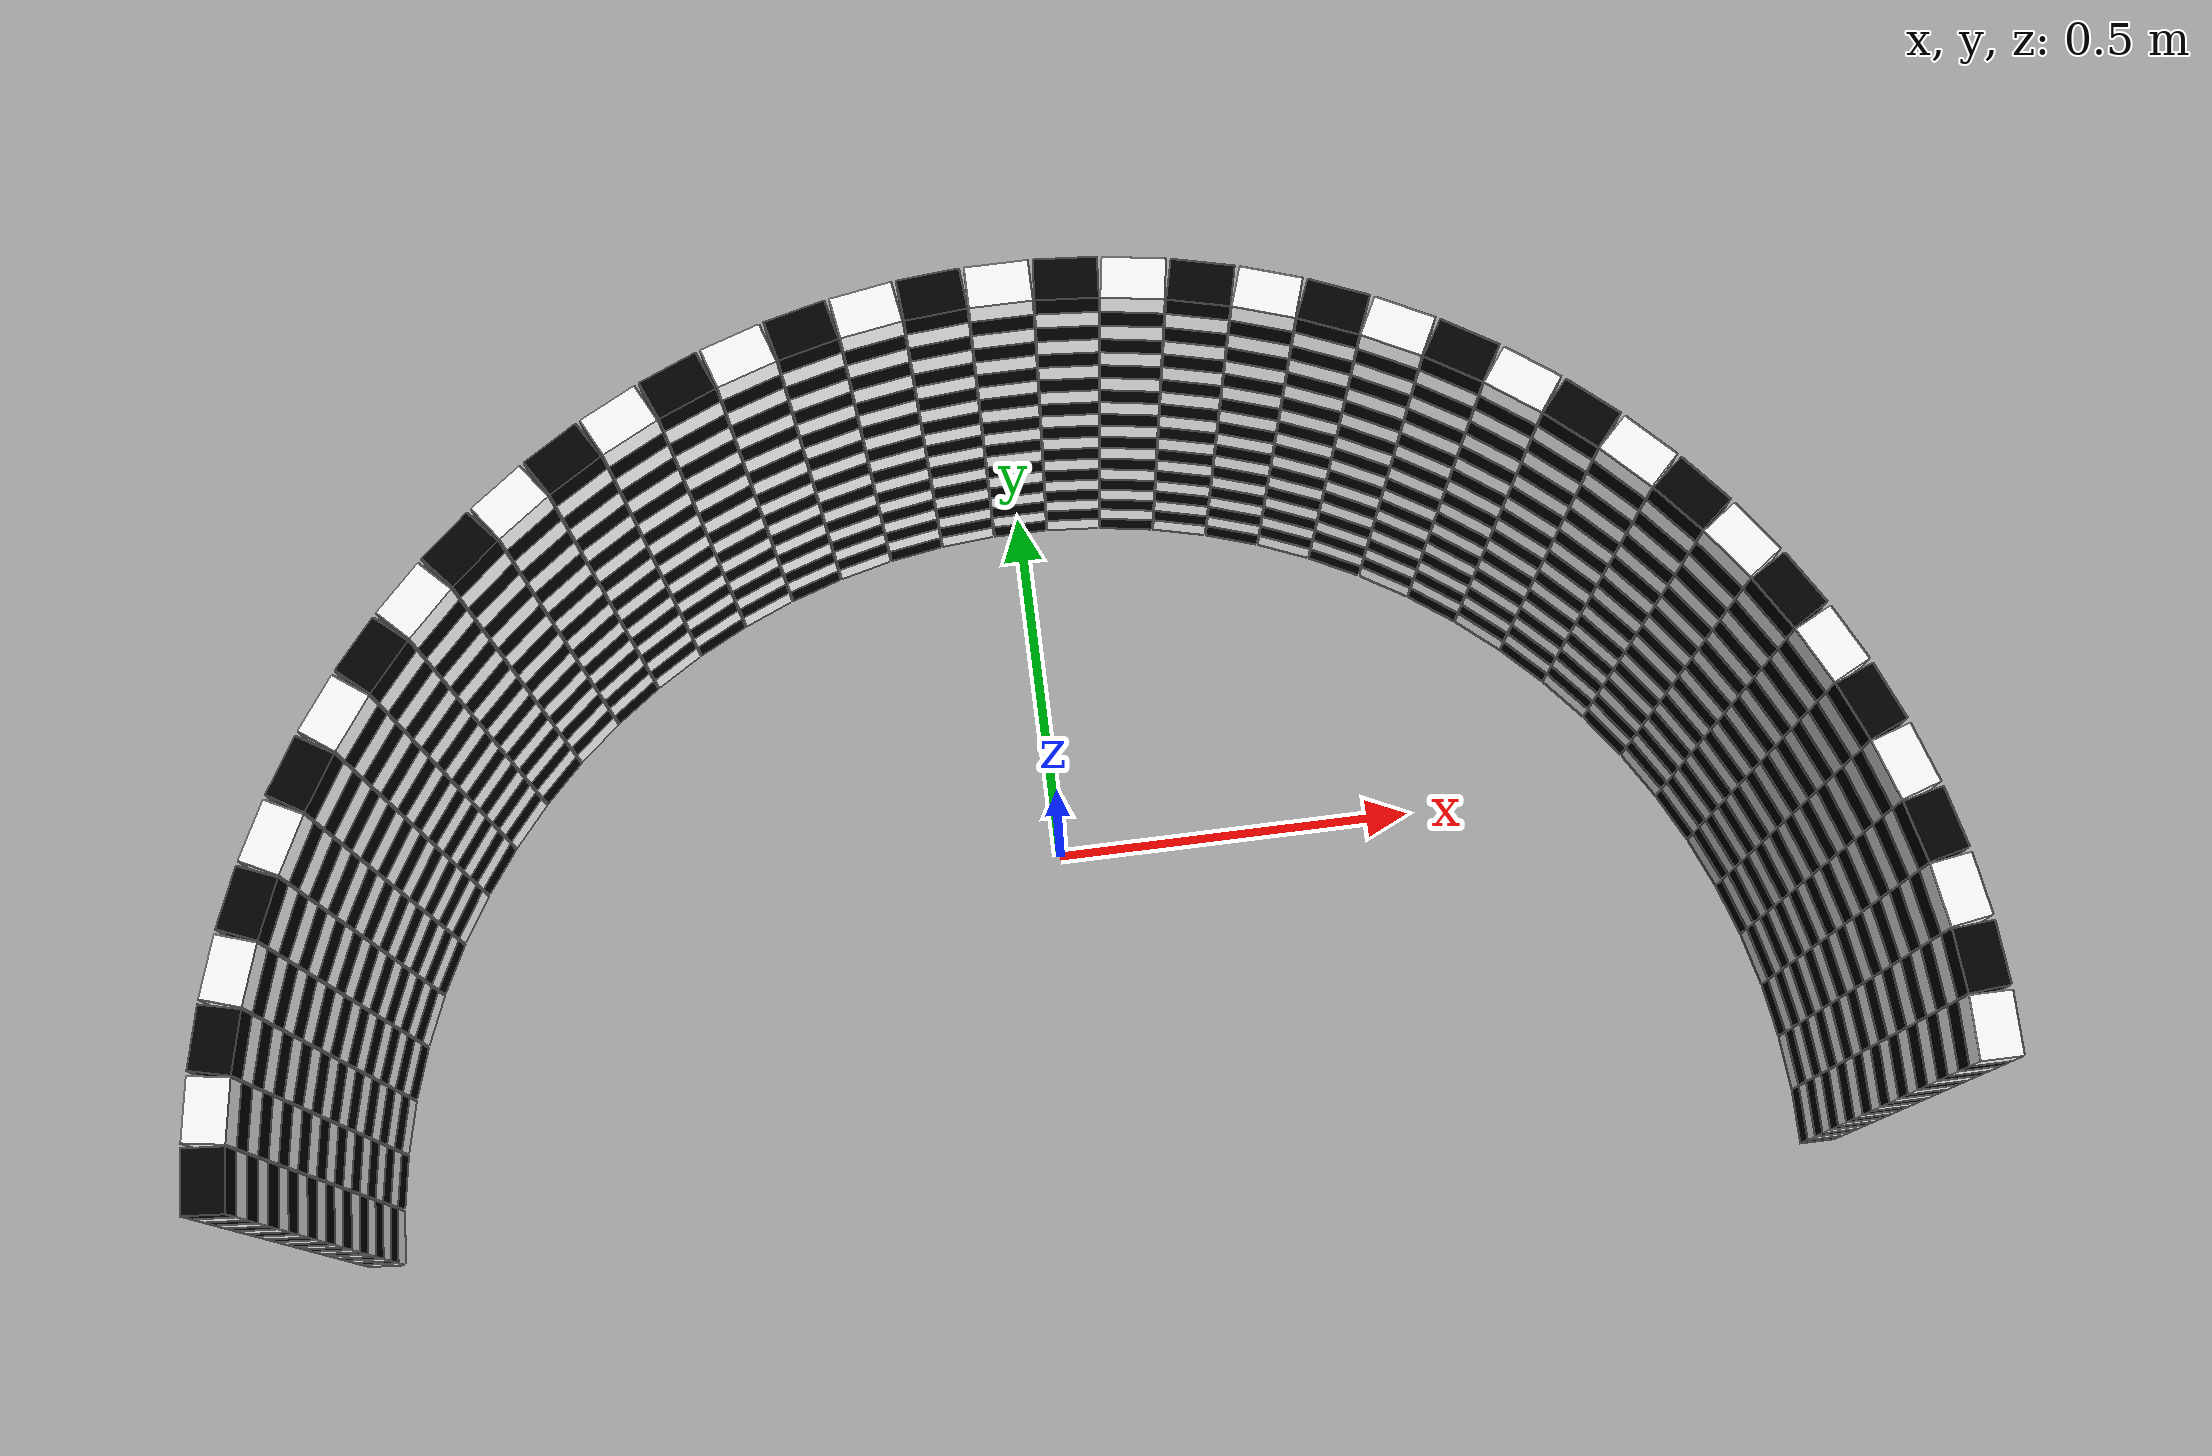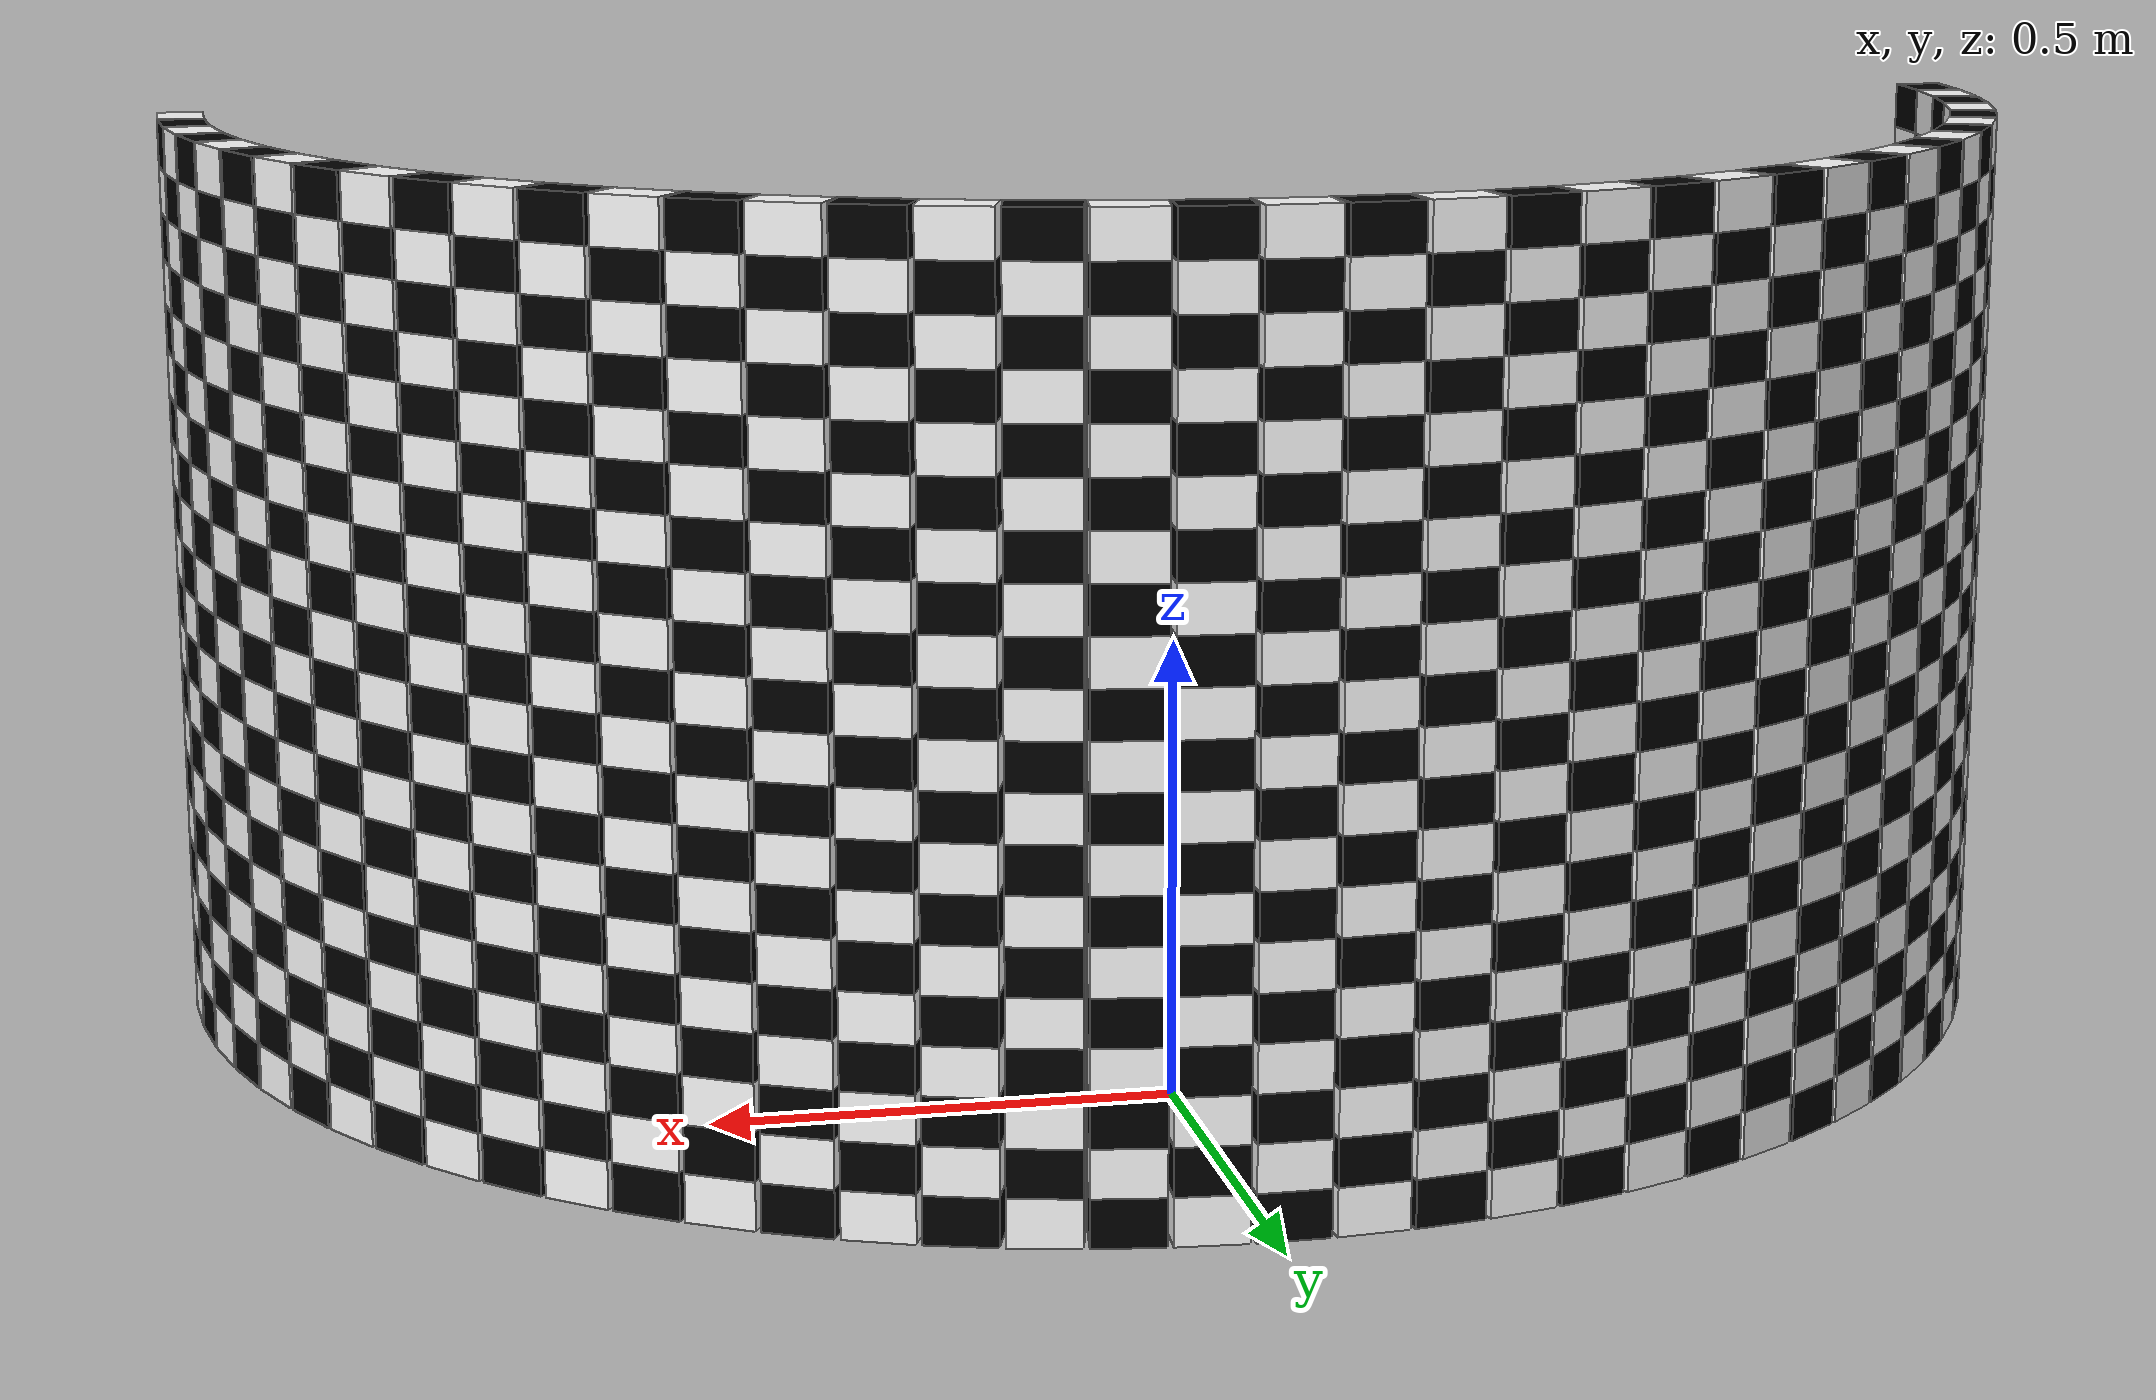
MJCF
<!-- This file was generated by curved_surface.py -->
<!-- It is not recommended to edit this file -->
<mujoco>
    <default>
        <geom density="100" friction=".5" rgba="1 .6 .8 1" />
    </default>
    <worldbody>
        <geom type="box" size=".025 0.037500000000000006 .025" pos="1.0 -0.5 1.0" euler="0 0 0.0" rgba="1 1 1 1" />
<geom type="box" size=".025 0.037500000000000006 .025" pos="0.996917333733128 -0.42154090427215507 1.0" euler="0 0 4.5" rgba="0 0 0 1" />
<geom type="box" size=".025 0.037500000000000006 .025" pos="0.9876883405951378 -0.34356553495976916 1.0" euler="0 0 9.0" rgba="1 1 1 1" />
<geom type="box" size=".025 0.037500000000000006 .025" pos="0.9723699203976766 -0.2665546361440946 1.0" euler="0 0 13.5" rgba="0 0 0 1" />
<geom type="box" size=".025 0.037500000000000006 .025" pos="0.9510565162951535 -0.19098300562505255 1.0" euler="0 0 18.0" rgba="1 1 1 1" />
<geom type="box" size=".025 0.037500000000000006 .025" pos="0.9238795325112867 -0.11731656763491016 1.0" euler="0 0 22.5" rgba="0 0 0 1" />
<geom type="box" size=".025 0.037500000000000006 .025" pos="0.8910065241883679 -0.04600950026045325 1.0" euler="0 0 27.0" rgba="1 1 1 1" />
<geom type="box" size=".025 0.037500000000000006 .025" pos="0.8526401643540923 0.0224985647159488 1.0" euler="0 0 31.5" rgba="0 0 0 1" />
<geom type="box" size=".025 0.037500000000000006 .025" pos="0.8090169943749475 0.08778525229247314 1.0" euler="0 0 36.0" rgba="1 1 1 1" />
<geom type="box" size=".025 0.037500000000000006 .025" pos="0.7604059656000309 0.14944804833018366 1.0" euler="0 0 40.5" rgba="0 0 0 1" />
<geom type="box" size=".025 0.037500000000000006 .025" pos="0.7071067811865476 0.20710678118654746 1.0" euler="0 0 45.0" rgba="1 1 1 1" />
<geom type="box" size=".025 0.037500000000000006 .025" pos="0.6494480483301837 0.26040596560003104 1.0" euler="0 0 49.5" rgba="0 0 0 1" />
<geom type="box" size=".025 0.037500000000000006 .025" pos="0.5877852522924731 0.30901699437494745 1.0" euler="0 0 54.0" rgba="1 1 1 1" />
<geom type="box" size=".025 0.037500000000000006 .025" pos="0.5224985647159489 0.3526401643540922 1.0" euler="0 0 58.5" rgba="0 0 0 1" />
<geom type="box" size=".025 0.037500000000000006 .025" pos="0.45399049973954675 0.3910065241883678 1.0" euler="0 0 63.0" rgba="1 1 1 1" />
<geom type="box" size=".025 0.037500000000000006 .025" pos="0.38268343236508984 0.42387953251128674 1.0" euler="0 0 67.5" rgba="0 0 0 1" />
<geom type="box" size=".025 0.037500000000000006 .025" pos="0.30901699437494745 0.45105651629515364 1.0" euler="0 0 72.0" rgba="1 1 1 1" />
<geom type="box" size=".025 0.037500000000000006 .025" pos="0.23344536385590553 0.47236992039767656 1.0" euler="0 0 76.5" rgba="0 0 0 1" />
<geom type="box" size=".025 0.037500000000000006 .025" pos="0.15643446504023095 0.48768834059513777 1.0" euler="0 0 81.0" rgba="1 1 1 1" />
<geom type="box" size=".025 0.037500000000000006 .025" pos="0.07845909572784504 0.4969173337331281 1.0" euler="0 0 85.5" rgba="0 0 0 1" />
<geom type="box" size=".025 0.037500000000000006 .025" pos="1.1102230246251565e-16 0.5 1.0" euler="0 0 90.0" rgba="1 1 1 1" />
<geom type="box" size=".025 0.037500000000000006 .025" pos="-0.07845909572784482 0.4969173337331281 1.0" euler="0 0 94.5" rgba="0 0 0 1" />
<geom type="box" size=".025 0.037500000000000006 .025" pos="-0.15643446504023073 0.48768834059513777 1.0" euler="0 0 99.0" rgba="1 1 1 1" />
<geom type="box" size=".025 0.037500000000000006 .025" pos="-0.2334453638559053 0.4723699203976768 1.0" euler="0 0 103.5" rgba="0 0 0 1" />
<geom type="box" size=".025 0.037500000000000006 .025" pos="-0.30901699437494745 0.45105651629515364 1.0" euler="0 0 108.0" rgba="1 1 1 1" />
<geom type="box" size=".025 0.037500000000000006 .025" pos="-0.3826834323650896 0.42387953251128674 1.0" euler="0 0 112.5" rgba="0 0 0 1" />
<geom type="box" size=".025 0.037500000000000006 .025" pos="-0.45399049973954675 0.3910065241883678 1.0" euler="0 0 117.0" rgba="1 1 1 1" />
<geom type="box" size=".025 0.037500000000000006 .025" pos="-0.5224985647159488 0.3526401643540922 1.0" euler="0 0 121.5" rgba="0 0 0 1" />
<geom type="box" size=".025 0.037500000000000006 .025" pos="-0.5877852522924729 0.30901699437494745 1.0" euler="0 0 126.0" rgba="1 1 1 1" />
<geom type="box" size=".025 0.037500000000000006 .025" pos="-0.6494480483301834 0.26040596560003104 1.0" euler="0 0 130.5" rgba="0 0 0 1" />
<geom type="box" size=".025 0.037500000000000006 .025" pos="-0.7071067811865475 0.20710678118654746 1.0" euler="0 0 135.0" rgba="1 1 1 1" />
<geom type="box" size=".025 0.037500000000000006 .025" pos="-0.760405965600031 0.14944804833018388 1.0" euler="0 0 139.5" rgba="0 0 0 1" />
<geom type="box" size=".025 0.037500000000000006 .025" pos="-0.8090169943749475 0.08778525229247336 1.0" euler="0 0 144.0" rgba="1 1 1 1" />
<geom type="box" size=".025 0.037500000000000006 .025" pos="-0.8526401643540922 0.0224985647159488 1.0" euler="0 0 148.5" rgba="0 0 0 1" />
<geom type="box" size=".025 0.037500000000000006 .025" pos="-0.8910065241883678 -0.04600950026045314 1.0" euler="0 0 153.0" rgba="1 1 1 1" />
<geom type="box" size=".025 0.037500000000000006 .025" pos="-0.9238795325112867 -0.11731656763491016 1.0" euler="0 0 157.5" rgba="0 0 0 1" />
<geom type="box" size=".025 0.037500000000000006 .025" pos="-0.9510565162951536 -0.19098300562505255 1.0" euler="0 0 162.0" rgba="1 1 1 1" />
<geom type="box" size=".025 0.037500000000000006 .025" pos="-0.9723699203976766 -0.26655463614409447 1.0" euler="0 0 166.5" rgba="0 0 0 1" />
<geom type="box" size=".025 0.037500000000000006 .025" pos="-0.9876883405951378 -0.34356553495976905 1.0" euler="0 0 171.0" rgba="1 1 1 1" />
<geom type="box" size=".025 0.037500000000000006 .025" pos="-0.9969173337331281 -0.42154090427215496 1.0" euler="0 0 175.5" rgba="0 0 0 1" />
<geom type="box" size=".025 0.037500000000000006 .025" pos="1.0 -0.5 0.95" euler="0 0 0.0" rgba="0 0 0 1" />
<geom type="box" size=".025 0.037500000000000006 .025" pos="0.996917333733128 -0.42154090427215507 0.95" euler="0 0 4.5" rgba="1 1 1 1" />
<geom type="box" size=".025 0.037500000000000006 .025" pos="0.9876883405951378 -0.34356553495976916 0.95" euler="0 0 9.0" rgba="0 0 0 1" />
<geom type="box" size=".025 0.037500000000000006 .025" pos="0.9723699203976766 -0.2665546361440946 0.95" euler="0 0 13.5" rgba="1 1 1 1" />
<geom type="box" size=".025 0.037500000000000006 .025" pos="0.9510565162951535 -0.19098300562505255 0.95" euler="0 0 18.0" rgba="0 0 0 1" />
<geom type="box" size=".025 0.037500000000000006 .025" pos="0.9238795325112867 -0.11731656763491016 0.95" euler="0 0 22.5" rgba="1 1 1 1" />
<geom type="box" size=".025 0.037500000000000006 .025" pos="0.8910065241883679 -0.04600950026045325 0.95" euler="0 0 27.0" rgba="0 0 0 1" />
<geom type="box" size=".025 0.037500000000000006 .025" pos="0.8526401643540923 0.0224985647159488 0.95" euler="0 0 31.5" rgba="1 1 1 1" />
<geom type="box" size=".025 0.037500000000000006 .025" pos="0.8090169943749475 0.08778525229247314 0.95" euler="0 0 36.0" rgba="0 0 0 1" />
<geom type="box" size=".025 0.037500000000000006 .025" pos="0.7604059656000309 0.14944804833018366 0.95" euler="0 0 40.5" rgba="1 1 1 1" />
<geom type="box" size=".025 0.037500000000000006 .025" pos="0.7071067811865476 0.20710678118654746 0.95" euler="0 0 45.0" rgba="0 0 0 1" />
<geom type="box" size=".025 0.037500000000000006 .025" pos="0.6494480483301837 0.26040596560003104 0.95" euler="0 0 49.5" rgba="1 1 1 1" />
<geom type="box" size=".025 0.037500000000000006 .025" pos="0.5877852522924731 0.30901699437494745 0.95" euler="0 0 54.0" rgba="0 0 0 1" />
<geom type="box" size=".025 0.037500000000000006 .025" pos="0.5224985647159489 0.3526401643540922 0.95" euler="0 0 58.5" rgba="1 1 1 1" />
<geom type="box" size=".025 0.037500000000000006 .025" pos="0.45399049973954675 0.3910065241883678 0.95" euler="0 0 63.0" rgba="0 0 0 1" />
<geom type="box" size=".025 0.037500000000000006 .025" pos="0.38268343236508984 0.42387953251128674 0.95" euler="0 0 67.5" rgba="1 1 1 1" />
<geom type="box" size=".025 0.037500000000000006 .025" pos="0.30901699437494745 0.45105651629515364 0.95" euler="0 0 72.0" rgba="0 0 0 1" />
<geom type="box" size=".025 0.037500000000000006 .025" pos="0.23344536385590553 0.47236992039767656 0.95" euler="0 0 76.5" rgba="1 1 1 1" />
<geom type="box" size=".025 0.037500000000000006 .025" pos="0.15643446504023095 0.48768834059513777 0.95" euler="0 0 81.0" rgba="0 0 0 1" />
<geom type="box" size=".025 0.037500000000000006 .025" pos="0.07845909572784504 0.4969173337331281 0.95" euler="0 0 85.5" rgba="1 1 1 1" />
<geom type="box" size=".025 0.037500000000000006 .025" pos="1.1102230246251565e-16 0.5 0.95" euler="0 0 90.0" rgba="0 0 0 1" />
<geom type="box" size=".025 0.037500000000000006 .025" pos="-0.07845909572784482 0.4969173337331281 0.95" euler="0 0 94.5" rgba="1 1 1 1" />
<geom type="box" size=".025 0.037500000000000006 .025" pos="-0.15643446504023073 0.48768834059513777 0.95" euler="0 0 99.0" rgba="0 0 0 1" />
<geom type="box" size=".025 0.037500000000000006 .025" pos="-0.2334453638559053 0.4723699203976768 0.95" euler="0 0 103.5" rgba="1 1 1 1" />
<geom type="box" size=".025 0.037500000000000006 .025" pos="-0.30901699437494745 0.45105651629515364 0.95" euler="0 0 108.0" rgba="0 0 0 1" />
<geom type="box" size=".025 0.037500000000000006 .025" pos="-0.3826834323650896 0.42387953251128674 0.95" euler="0 0 112.5" rgba="1 1 1 1" />
<geom type="box" size=".025 0.037500000000000006 .025" pos="-0.45399049973954675 0.3910065241883678 0.95" euler="0 0 117.0" rgba="0 0 0 1" />
<geom type="box" size=".025 0.037500000000000006 .025" pos="-0.5224985647159488 0.3526401643540922 0.95" euler="0 0 121.5" rgba="1 1 1 1" />
<geom type="box" size=".025 0.037500000000000006 .025" pos="-0.5877852522924729 0.30901699437494745 0.95" euler="0 0 126.0" rgba="0 0 0 1" />
<geom type="box" size=".025 0.037500000000000006 .025" pos="-0.6494480483301834 0.26040596560003104 0.95" euler="0 0 130.5" rgba="1 1 1 1" />
<geom type="box" size=".025 0.037500000000000006 .025" pos="-0.7071067811865475 0.20710678118654746 0.95" euler="0 0 135.0" rgba="0 0 0 1" />
<geom type="box" size=".025 0.037500000000000006 .025" pos="-0.760405965600031 0.14944804833018388 0.95" euler="0 0 139.5" rgba="1 1 1 1" />
<geom type="box" size=".025 0.037500000000000006 .025" pos="-0.8090169943749475 0.08778525229247336 0.95" euler="0 0 144.0" rgba="0 0 0 1" />
<geom type="box" size=".025 0.037500000000000006 .025" pos="-0.8526401643540922 0.0224985647159488 0.95" euler="0 0 148.5" rgba="1 1 1 1" />
<geom type="box" size=".025 0.037500000000000006 .025" pos="-0.8910065241883678 -0.04600950026045314 0.95" euler="0 0 153.0" rgba="0 0 0 1" />
<geom type="box" size=".025 0.037500000000000006 .025" pos="-0.9238795325112867 -0.11731656763491016 0.95" euler="0 0 157.5" rgba="1 1 1 1" />
<geom type="box" size=".025 0.037500000000000006 .025" pos="-0.9510565162951536 -0.19098300562505255 0.95" euler="0 0 162.0" rgba="0 0 0 1" />
<geom type="box" size=".025 0.037500000000000006 .025" pos="-0.9723699203976766 -0.26655463614409447 0.95" euler="0 0 166.5" rgba="1 1 1 1" />
<geom type="box" size=".025 0.037500000000000006 .025" pos="-0.9876883405951378 -0.34356553495976905 0.95" euler="0 0 171.0" rgba="0 0 0 1" />
<geom type="box" size=".025 0.037500000000000006 .025" pos="-0.9969173337331281 -0.42154090427215496 0.95" euler="0 0 175.5" rgba="1 1 1 1" />
<geom type="box" size=".025 0.037500000000000006 .025" pos="1.0 -0.5 0.9" euler="0 0 0.0" rgba="1 1 1 1" />
<geom type="box" size=".025 0.037500000000000006 .025" pos="0.996917333733128 -0.42154090427215507 0.9" euler="0 0 4.5" rgba="0 0 0 1" />
<geom type="box" size=".025 0.037500000000000006 .025" pos="0.9876883405951378 -0.34356553495976916 0.9" euler="0 0 9.0" rgba="1 1 1 1" />
<geom type="box" size=".025 0.037500000000000006 .025" pos="0.9723699203976766 -0.2665546361440946 0.9" euler="0 0 13.5" rgba="0 0 0 1" />
<geom type="box" size=".025 0.037500000000000006 .025" pos="0.9510565162951535 -0.19098300562505255 0.9" euler="0 0 18.0" rgba="1 1 1 1" />
<geom type="box" size=".025 0.037500000000000006 .025" pos="0.9238795325112867 -0.11731656763491016 0.9" euler="0 0 22.5" rgba="0 0 0 1" />
<geom type="box" size=".025 0.037500000000000006 .025" pos="0.8910065241883679 -0.04600950026045325 0.9" euler="0 0 27.0" rgba="1 1 1 1" />
<geom type="box" size=".025 0.037500000000000006 .025" pos="0.8526401643540923 0.0224985647159488 0.9" euler="0 0 31.5" rgba="0 0 0 1" />
<geom type="box" size=".025 0.037500000000000006 .025" pos="0.8090169943749475 0.08778525229247314 0.9" euler="0 0 36.0" rgba="1 1 1 1" />
<geom type="box" size=".025 0.037500000000000006 .025" pos="0.7604059656000309 0.14944804833018366 0.9" euler="0 0 40.5" rgba="0 0 0 1" />
<geom type="box" size=".025 0.037500000000000006 .025" pos="0.7071067811865476 0.20710678118654746 0.9" euler="0 0 45.0" rgba="1 1 1 1" />
<geom type="box" size=".025 0.037500000000000006 .025" pos="0.6494480483301837 0.26040596560003104 0.9" euler="0 0 49.5" rgba="0 0 0 1" />
<geom type="box" size=".025 0.037500000000000006 .025" pos="0.5877852522924731 0.30901699437494745 0.9" euler="0 0 54.0" rgba="1 1 1 1" />
<geom type="box" size=".025 0.037500000000000006 .025" pos="0.5224985647159489 0.3526401643540922 0.9" euler="0 0 58.5" rgba="0 0 0 1" />
<geom type="box" size=".025 0.037500000000000006 .025" pos="0.45399049973954675 0.3910065241883678 0.9" euler="0 0 63.0" rgba="1 1 1 1" />
<geom type="box" size=".025 0.037500000000000006 .025" pos="0.38268343236508984 0.42387953251128674 0.9" euler="0 0 67.5" rgba="0 0 0 1" />
<geom type="box" size=".025 0.037500000000000006 .025" pos="0.30901699437494745 0.45105651629515364 0.9" euler="0 0 72.0" rgba="1 1 1 1" />
<geom type="box" size=".025 0.037500000000000006 .025" pos="0.23344536385590553 0.47236992039767656 0.9" euler="0 0 76.5" rgba="0 0 0 1" />
<geom type="box" size=".025 0.037500000000000006 .025" pos="0.15643446504023095 0.48768834059513777 0.9" euler="0 0 81.0" rgba="1 1 1 1" />
<geom type="box" size=".025 0.037500000000000006 .025" pos="0.07845909572784504 0.4969173337331281 0.9" euler="0 0 85.5" rgba="0 0 0 1" />
<geom type="box" size=".025 0.037500000000000006 .025" pos="1.1102230246251565e-16 0.5 0.9" euler="0 0 90.0" rgba="1 1 1 1" />
<geom type="box" size=".025 0.037500000000000006 .025" pos="-0.07845909572784482 0.4969173337331281 0.9" euler="0 0 94.5" rgba="0 0 0 1" />
<geom type="box" size=".025 0.037500000000000006 .025" pos="-0.15643446504023073 0.48768834059513777 0.9" euler="0 0 99.0" rgba="1 1 1 1" />
<geom type="box" size=".025 0.037500000000000006 .025" pos="-0.2334453638559053 0.4723699203976768 0.9" euler="0 0 103.5" rgba="0 0 0 1" />
<geom type="box" size=".025 0.037500000000000006 .025" pos="-0.30901699437494745 0.45105651629515364 0.9" euler="0 0 108.0" rgba="1 1 1 1" />
<geom type="box" size=".025 0.037500000000000006 .025" pos="-0.3826834323650896 0.42387953251128674 0.9" euler="0 0 112.5" rgba="0 0 0 1" />
<geom type="box" size=".025 0.037500000000000006 .025" pos="-0.45399049973954675 0.3910065241883678 0.9" euler="0 0 117.0" rgba="1 1 1 1" />
<geom type="box" size=".025 0.037500000000000006 .025" pos="-0.5224985647159488 0.3526401643540922 0.9" euler="0 0 121.5" rgba="0 0 0 1" />
<geom type="box" size=".025 0.037500000000000006 .025" pos="-0.5877852522924729 0.30901699437494745 0.9" euler="0 0 126.0" rgba="1 1 1 1" />
<geom type="box" size=".025 0.037500000000000006 .025" pos="-0.6494480483301834 0.26040596560003104 0.9" euler="0 0 130.5" rgba="0 0 0 1" />
<geom type="box" size=".025 0.037500000000000006 .025" pos="-0.7071067811865475 0.20710678118654746 0.9" euler="0 0 135.0" rgba="1 1 1 1" />
<geom type="box" size=".025 0.037500000000000006 .025" pos="-0.760405965600031 0.14944804833018388 0.9" euler="0 0 139.5" rgba="0 0 0 1" />
<geom type="box" size=".025 0.037500000000000006 .025" pos="-0.8090169943749475 0.08778525229247336 0.9" euler="0 0 144.0" rgba="1 1 1 1" />
<geom type="box" size=".025 0.037500000000000006 .025" pos="-0.8526401643540922 0.0224985647159488 0.9" euler="0 0 148.5" rgba="0 0 0 1" />
<geom type="box" size=".025 0.037500000000000006 .025" pos="-0.8910065241883678 -0.04600950026045314 0.9" euler="0 0 153.0" rgba="1 1 1 1" />
<geom type="box" size=".025 0.037500000000000006 .025" pos="-0.9238795325112867 -0.11731656763491016 0.9" euler="0 0 157.5" rgba="0 0 0 1" />
<geom type="box" size=".025 0.037500000000000006 .025" pos="-0.9510565162951536 -0.19098300562505255 0.9" euler="0 0 162.0" rgba="1 1 1 1" />
<geom type="box" size=".025 0.037500000000000006 .025" pos="-0.9723699203976766 -0.26655463614409447 0.9" euler="0 0 166.5" rgba="0 0 0 1" />
<geom type="box" size=".025 0.037500000000000006 .025" pos="-0.9876883405951378 -0.34356553495976905 0.9" euler="0 0 171.0" rgba="1 1 1 1" />
<geom type="box" size=".025 0.037500000000000006 .025" pos="-0.9969173337331281 -0.42154090427215496 0.9" euler="0 0 175.5" rgba="0 0 0 1" />
<geom type="box" size=".025 0.037500000000000006 .025" pos="1.0 -0.5 0.85" euler="0 0 0.0" rgba="0 0 0 1" />
<geom type="box" size=".025 0.037500000000000006 .025" pos="0.996917333733128 -0.42154090427215507 0.85" euler="0 0 4.5" rgba="1 1 1 1" />
<geom type="box" size=".025 0.037500000000000006 .025" pos="0.9876883405951378 -0.34356553495976916 0.85" euler="0 0 9.0" rgba="0 0 0 1" />
<geom type="box" size=".025 0.037500000000000006 .025" pos="0.9723699203976766 -0.2665546361440946 0.85" euler="0 0 13.5" rgba="1 1 1 1" />
<geom type="box" size=".025 0.037500000000000006 .025" pos="0.9510565162951535 -0.19098300562505255 0.85" euler="0 0 18.0" rgba="0 0 0 1" />
<geom type="box" size=".025 0.037500000000000006 .025" pos="0.9238795325112867 -0.11731656763491016 0.85" euler="0 0 22.5" rgba="1 1 1 1" />
<geom type="box" size=".025 0.037500000000000006 .025" pos="0.8910065241883679 -0.04600950026045325 0.85" euler="0 0 27.0" rgba="0 0 0 1" />
<geom type="box" size=".025 0.037500000000000006 .025" pos="0.8526401643540923 0.0224985647159488 0.85" euler="0 0 31.5" rgba="1 1 1 1" />
<geom type="box" size=".025 0.037500000000000006 .025" pos="0.8090169943749475 0.08778525229247314 0.85" euler="0 0 36.0" rgba="0 0 0 1" />
<geom type="box" size=".025 0.037500000000000006 .025" pos="0.7604059656000309 0.14944804833018366 0.85" euler="0 0 40.5" rgba="1 1 1 1" />
<geom type="box" size=".025 0.037500000000000006 .025" pos="0.7071067811865476 0.20710678118654746 0.85" euler="0 0 45.0" rgba="0 0 0 1" />
<geom type="box" size=".025 0.037500000000000006 .025" pos="0.6494480483301837 0.26040596560003104 0.85" euler="0 0 49.5" rgba="1 1 1 1" />
<geom type="box" size=".025 0.037500000000000006 .025" pos="0.5877852522924731 0.30901699437494745 0.85" euler="0 0 54.0" rgba="0 0 0 1" />
<geom type="box" size=".025 0.037500000000000006 .025" pos="0.5224985647159489 0.3526401643540922 0.85" euler="0 0 58.5" rgba="1 1 1 1" />
<geom type="box" size=".025 0.037500000000000006 .025" pos="0.45399049973954675 0.3910065241883678 0.85" euler="0 0 63.0" rgba="0 0 0 1" />
<geom type="box" size=".025 0.037500000000000006 .025" pos="0.38268343236508984 0.42387953251128674 0.85" euler="0 0 67.5" rgba="1 1 1 1" />
<geom type="box" size=".025 0.037500000000000006 .025" pos="0.30901699437494745 0.45105651629515364 0.85" euler="0 0 72.0" rgba="0 0 0 1" />
<geom type="box" size=".025 0.037500000000000006 .025" pos="0.23344536385590553 0.47236992039767656 0.85" euler="0 0 76.5" rgba="1 1 1 1" />
<geom type="box" size=".025 0.037500000000000006 .025" pos="0.15643446504023095 0.48768834059513777 0.85" euler="0 0 81.0" rgba="0 0 0 1" />
<geom type="box" size=".025 0.037500000000000006 .025" pos="0.07845909572784504 0.4969173337331281 0.85" euler="0 0 85.5" rgba="1 1 1 1" />
<geom type="box" size=".025 0.037500000000000006 .025" pos="1.1102230246251565e-16 0.5 0.85" euler="0 0 90.0" rgba="0 0 0 1" />
<geom type="box" size=".025 0.037500000000000006 .025" pos="-0.07845909572784482 0.4969173337331281 0.85" euler="0 0 94.5" rgba="1 1 1 1" />
<geom type="box" size=".025 0.037500000000000006 .025" pos="-0.15643446504023073 0.48768834059513777 0.85" euler="0 0 99.0" rgba="0 0 0 1" />
<geom type="box" size=".025 0.037500000000000006 .025" pos="-0.2334453638559053 0.4723699203976768 0.85" euler="0 0 103.5" rgba="1 1 1 1" />
<geom type="box" size=".025 0.037500000000000006 .025" pos="-0.30901699437494745 0.45105651629515364 0.85" euler="0 0 108.0" rgba="0 0 0 1" />
<geom type="box" size=".025 0.037500000000000006 .025" pos="-0.3826834323650896 0.42387953251128674 0.85" euler="0 0 112.5" rgba="1 1 1 1" />
<geom type="box" size=".025 0.037500000000000006 .025" pos="-0.45399049973954675 0.3910065241883678 0.85" euler="0 0 117.0" rgba="0 0 0 1" />
<geom type="box" size=".025 0.037500000000000006 .025" pos="-0.5224985647159488 0.3526401643540922 0.85" euler="0 0 121.5" rgba="1 1 1 1" />
<geom type="box" size=".025 0.037500000000000006 .025" pos="-0.5877852522924729 0.30901699437494745 0.85" euler="0 0 126.0" rgba="0 0 0 1" />
<geom type="box" size=".025 0.037500000000000006 .025" pos="-0.6494480483301834 0.26040596560003104 0.85" euler="0 0 130.5" rgba="1 1 1 1" />
<geom type="box" size=".025 0.037500000000000006 .025" pos="-0.7071067811865475 0.20710678118654746 0.85" euler="0 0 135.0" rgba="0 0 0 1" />
<geom type="box" size=".025 0.037500000000000006 .025" pos="-0.760405965600031 0.14944804833018388 0.85" euler="0 0 139.5" rgba="1 1 1 1" />
<geom type="box" size=".025 0.037500000000000006 .025" pos="-0.8090169943749475 0.08778525229247336 0.85" euler="0 0 144.0" rgba="0 0 0 1" />
<geom type="box" size=".025 0.037500000000000006 .025" pos="-0.8526401643540922 0.0224985647159488 0.85" euler="0 0 148.5" rgba="1 1 1 1" />
<geom type="box" size=".025 0.037500000000000006 .025" pos="-0.8910065241883678 -0.04600950026045314 0.85" euler="0 0 153.0" rgba="0 0 0 1" />
<geom type="box" size=".025 0.037500000000000006 .025" pos="-0.9238795325112867 -0.11731656763491016 0.85" euler="0 0 157.5" rgba="1 1 1 1" />
<geom type="box" size=".025 0.037500000000000006 .025" pos="-0.9510565162951536 -0.19098300562505255 0.85" euler="0 0 162.0" rgba="0 0 0 1" />
<geom type="box" size=".025 0.037500000000000006 .025" pos="-0.9723699203976766 -0.26655463614409447 0.85" euler="0 0 166.5" rgba="1 1 1 1" />
<geom type="box" size=".025 0.037500000000000006 .025" pos="-0.9876883405951378 -0.34356553495976905 0.85" euler="0 0 171.0" rgba="0 0 0 1" />
<geom type="box" size=".025 0.037500000000000006 .025" pos="-0.9969173337331281 -0.42154090427215496 0.85" euler="0 0 175.5" rgba="1 1 1 1" />
<geom type="box" size=".025 0.037500000000000006 .025" pos="1.0 -0.5 0.8" euler="0 0 0.0" rgba="1 1 1 1" />
<geom type="box" size=".025 0.037500000000000006 .025" pos="0.996917333733128 -0.42154090427215507 0.8" euler="0 0 4.5" rgba="0 0 0 1" />
<geom type="box" size=".025 0.037500000000000006 .025" pos="0.9876883405951378 -0.34356553495976916 0.8" euler="0 0 9.0" rgba="1 1 1 1" />
<geom type="box" size=".025 0.037500000000000006 .025" pos="0.9723699203976766 -0.2665546361440946 0.8" euler="0 0 13.5" rgba="0 0 0 1" />
<geom type="box" size=".025 0.037500000000000006 .025" pos="0.9510565162951535 -0.19098300562505255 0.8" euler="0 0 18.0" rgba="1 1 1 1" />
<geom type="box" size=".025 0.037500000000000006 .025" pos="0.9238795325112867 -0.11731656763491016 0.8" euler="0 0 22.5" rgba="0 0 0 1" />
<geom type="box" size=".025 0.037500000000000006 .025" pos="0.8910065241883679 -0.04600950026045325 0.8" euler="0 0 27.0" rgba="1 1 1 1" />
<geom type="box" size=".025 0.037500000000000006 .025" pos="0.8526401643540923 0.0224985647159488 0.8" euler="0 0 31.5" rgba="0 0 0 1" />
<geom type="box" size=".025 0.037500000000000006 .025" pos="0.8090169943749475 0.08778525229247314 0.8" euler="0 0 36.0" rgba="1 1 1 1" />
<geom type="box" size=".025 0.037500000000000006 .025" pos="0.7604059656000309 0.14944804833018366 0.8" euler="0 0 40.5" rgba="0 0 0 1" />
<geom type="box" size=".025 0.037500000000000006 .025" pos="0.7071067811865476 0.20710678118654746 0.8" euler="0 0 45.0" rgba="1 1 1 1" />
<geom type="box" size=".025 0.037500000000000006 .025" pos="0.6494480483301837 0.26040596560003104 0.8" euler="0 0 49.5" rgba="0 0 0 1" />
<geom type="box" size=".025 0.037500000000000006 .025" pos="0.5877852522924731 0.30901699437494745 0.8" euler="0 0 54.0" rgba="1 1 1 1" />
<geom type="box" size=".025 0.037500000000000006 .025" pos="0.5224985647159489 0.3526401643540922 0.8" euler="0 0 58.5" rgba="0 0 0 1" />
<geom type="box" size=".025 0.037500000000000006 .025" pos="0.45399049973954675 0.3910065241883678 0.8" euler="0 0 63.0" rgba="1 1 1 1" />
<geom type="box" size=".025 0.037500000000000006 .025" pos="0.38268343236508984 0.42387953251128674 0.8" euler="0 0 67.5" rgba="0 0 0 1" />
<geom type="box" size=".025 0.037500000000000006 .025" pos="0.30901699437494745 0.45105651629515364 0.8" euler="0 0 72.0" rgba="1 1 1 1" />
<geom type="box" size=".025 0.037500000000000006 .025" pos="0.23344536385590553 0.47236992039767656 0.8" euler="0 0 76.5" rgba="0 0 0 1" />
<geom type="box" size=".025 0.037500000000000006 .025" pos="0.15643446504023095 0.48768834059513777 0.8" euler="0 0 81.0" rgba="1 1 1 1" />
<geom type="box" size=".025 0.037500000000000006 .025" pos="0.07845909572784504 0.4969173337331281 0.8" euler="0 0 85.5" rgba="0 0 0 1" />
<geom type="box" size=".025 0.037500000000000006 .025" pos="1.1102230246251565e-16 0.5 0.8" euler="0 0 90.0" rgba="1 1 1 1" />
<geom type="box" size=".025 0.037500000000000006 .025" pos="-0.07845909572784482 0.4969173337331281 0.8" euler="0 0 94.5" rgba="0 0 0 1" />
<geom type="box" size=".025 0.037500000000000006 .025" pos="-0.15643446504023073 0.48768834059513777 0.8" euler="0 0 99.0" rgba="1 1 1 1" />
<geom type="box" size=".025 0.037500000000000006 .025" pos="-0.2334453638559053 0.4723699203976768 0.8" euler="0 0 103.5" rgba="0 0 0 1" />
<geom type="box" size=".025 0.037500000000000006 .025" pos="-0.30901699437494745 0.45105651629515364 0.8" euler="0 0 108.0" rgba="1 1 1 1" />
<geom type="box" size=".025 0.037500000000000006 .025" pos="-0.3826834323650896 0.42387953251128674 0.8" euler="0 0 112.5" rgba="0 0 0 1" />
<geom type="box" size=".025 0.037500000000000006 .025" pos="-0.45399049973954675 0.3910065241883678 0.8" euler="0 0 117.0" rgba="1 1 1 1" />
<geom type="box" size=".025 0.037500000000000006 .025" pos="-0.5224985647159488 0.3526401643540922 0.8" euler="0 0 121.5" rgba="0 0 0 1" />
<geom type="box" size=".025 0.037500000000000006 .025" pos="-0.5877852522924729 0.30901699437494745 0.8" euler="0 0 126.0" rgba="1 1 1 1" />
<geom type="box" size=".025 0.037500000000000006 .025" pos="-0.6494480483301834 0.26040596560003104 0.8" euler="0 0 130.5" rgba="0 0 0 1" />
<geom type="box" size=".025 0.037500000000000006 .025" pos="-0.7071067811865475 0.20710678118654746 0.8" euler="0 0 135.0" rgba="1 1 1 1" />
<geom type="box" size=".025 0.037500000000000006 .025" pos="-0.760405965600031 0.14944804833018388 0.8" euler="0 0 139.5" rgba="0 0 0 1" />
<geom type="box" size=".025 0.037500000000000006 .025" pos="-0.8090169943749475 0.08778525229247336 0.8" euler="0 0 144.0" rgba="1 1 1 1" />
<geom type="box" size=".025 0.037500000000000006 .025" pos="-0.8526401643540922 0.0224985647159488 0.8" euler="0 0 148.5" rgba="0 0 0 1" />
<geom type="box" size=".025 0.037500000000000006 .025" pos="-0.8910065241883678 -0.04600950026045314 0.8" euler="0 0 153.0" rgba="1 1 1 1" />
<geom type="box" size=".025 0.037500000000000006 .025" pos="-0.9238795325112867 -0.11731656763491016 0.8" euler="0 0 157.5" rgba="0 0 0 1" />
<geom type="box" size=".025 0.037500000000000006 .025" pos="-0.9510565162951536 -0.19098300562505255 0.8" euler="0 0 162.0" rgba="1 1 1 1" />
<geom type="box" size=".025 0.037500000000000006 .025" pos="-0.9723699203976766 -0.26655463614409447 0.8" euler="0 0 166.5" rgba="0 0 0 1" />
<geom type="box" size=".025 0.037500000000000006 .025" pos="-0.9876883405951378 -0.34356553495976905 0.8" euler="0 0 171.0" rgba="1 1 1 1" />
<geom type="box" size=".025 0.037500000000000006 .025" pos="-0.9969173337331281 -0.42154090427215496 0.8" euler="0 0 175.5" rgba="0 0 0 1" />
<geom type="box" size=".025 0.037500000000000006 .025" pos="1.0 -0.5 0.75" euler="0 0 0.0" rgba="0 0 0 1" />
<geom type="box" size=".025 0.037500000000000006 .025" pos="0.996917333733128 -0.42154090427215507 0.75" euler="0 0 4.5" rgba="1 1 1 1" />
<geom type="box" size=".025 0.037500000000000006 .025" pos="0.9876883405951378 -0.34356553495976916 0.75" euler="0 0 9.0" rgba="0 0 0 1" />
<geom type="box" size=".025 0.037500000000000006 .025" pos="0.9723699203976766 -0.2665546361440946 0.75" euler="0 0 13.5" rgba="1 1 1 1" />
<geom type="box" size=".025 0.037500000000000006 .025" pos="0.9510565162951535 -0.19098300562505255 0.75" euler="0 0 18.0" rgba="0 0 0 1" />
<geom type="box" size=".025 0.037500000000000006 .025" pos="0.9238795325112867 -0.11731656763491016 0.75" euler="0 0 22.5" rgba="1 1 1 1" />
<geom type="box" size=".025 0.037500000000000006 .025" pos="0.8910065241883679 -0.04600950026045325 0.75" euler="0 0 27.0" rgba="0 0 0 1" />
<geom type="box" size=".025 0.037500000000000006 .025" pos="0.8526401643540923 0.0224985647159488 0.75" euler="0 0 31.5" rgba="1 1 1 1" />
<geom type="box" size=".025 0.037500000000000006 .025" pos="0.8090169943749475 0.08778525229247314 0.75" euler="0 0 36.0" rgba="0 0 0 1" />
<geom type="box" size=".025 0.037500000000000006 .025" pos="0.7604059656000309 0.14944804833018366 0.75" euler="0 0 40.5" rgba="1 1 1 1" />
<geom type="box" size=".025 0.037500000000000006 .025" pos="0.7071067811865476 0.20710678118654746 0.75" euler="0 0 45.0" rgba="0 0 0 1" />
<geom type="box" size=".025 0.037500000000000006 .025" pos="0.6494480483301837 0.26040596560003104 0.75" euler="0 0 49.5" rgba="1 1 1 1" />
<geom type="box" size=".025 0.037500000000000006 .025" pos="0.5877852522924731 0.30901699437494745 0.75" euler="0 0 54.0" rgba="0 0 0 1" />
<geom type="box" size=".025 0.037500000000000006 .025" pos="0.5224985647159489 0.3526401643540922 0.75" euler="0 0 58.5" rgba="1 1 1 1" />
<geom type="box" size=".025 0.037500000000000006 .025" pos="0.45399049973954675 0.3910065241883678 0.75" euler="0 0 63.0" rgba="0 0 0 1" />
<geom type="box" size=".025 0.037500000000000006 .025" pos="0.38268343236508984 0.42387953251128674 0.75" euler="0 0 67.5" rgba="1 1 1 1" />
<geom type="box" size=".025 0.037500000000000006 .025" pos="0.30901699437494745 0.45105651629515364 0.75" euler="0 0 72.0" rgba="0 0 0 1" />
<geom type="box" size=".025 0.037500000000000006 .025" pos="0.23344536385590553 0.47236992039767656 0.75" euler="0 0 76.5" rgba="1 1 1 1" />
<geom type="box" size=".025 0.037500000000000006 .025" pos="0.15643446504023095 0.48768834059513777 0.75" euler="0 0 81.0" rgba="0 0 0 1" />
<geom type="box" size=".025 0.037500000000000006 .025" pos="0.07845909572784504 0.4969173337331281 0.75" euler="0 0 85.5" rgba="1 1 1 1" />
<geom type="box" size=".025 0.037500000000000006 .025" pos="1.1102230246251565e-16 0.5 0.75" euler="0 0 90.0" rgba="0 0 0 1" />
<geom type="box" size=".025 0.037500000000000006 .025" pos="-0.07845909572784482 0.4969173337331281 0.75" euler="0 0 94.5" rgba="1 1 1 1" />
<geom type="box" size=".025 0.037500000000000006 .025" pos="-0.15643446504023073 0.48768834059513777 0.75" euler="0 0 99.0" rgba="0 0 0 1" />
<geom type="box" size=".025 0.037500000000000006 .025" pos="-0.2334453638559053 0.4723699203976768 0.75" euler="0 0 103.5" rgba="1 1 1 1" />
<geom type="box" size=".025 0.037500000000000006 .025" pos="-0.30901699437494745 0.45105651629515364 0.75" euler="0 0 108.0" rgba="0 0 0 1" />
<geom type="box" size=".025 0.037500000000000006 .025" pos="-0.3826834323650896 0.42387953251128674 0.75" euler="0 0 112.5" rgba="1 1 1 1" />
<geom type="box" size=".025 0.037500000000000006 .025" pos="-0.45399049973954675 0.3910065241883678 0.75" euler="0 0 117.0" rgba="0 0 0 1" />
<geom type="box" size=".025 0.037500000000000006 .025" pos="-0.5224985647159488 0.3526401643540922 0.75" euler="0 0 121.5" rgba="1 1 1 1" />
<geom type="box" size=".025 0.037500000000000006 .025" pos="-0.5877852522924729 0.30901699437494745 0.75" euler="0 0 126.0" rgba="0 0 0 1" />
<geom type="box" size=".025 0.037500000000000006 .025" pos="-0.6494480483301834 0.26040596560003104 0.75" euler="0 0 130.5" rgba="1 1 1 1" />
<geom type="box" size=".025 0.037500000000000006 .025" pos="-0.7071067811865475 0.20710678118654746 0.75" euler="0 0 135.0" rgba="0 0 0 1" />
<geom type="box" size=".025 0.037500000000000006 .025" pos="-0.760405965600031 0.14944804833018388 0.75" euler="0 0 139.5" rgba="1 1 1 1" />
<geom type="box" size=".025 0.037500000000000006 .025" pos="-0.8090169943749475 0.08778525229247336 0.75" euler="0 0 144.0" rgba="0 0 0 1" />
<geom type="box" size=".025 0.037500000000000006 .025" pos="-0.8526401643540922 0.0224985647159488 0.75" euler="0 0 148.5" rgba="1 1 1 1" />
<geom type="box" size=".025 0.037500000000000006 .025" pos="-0.8910065241883678 -0.04600950026045314 0.75" euler="0 0 153.0" rgba="0 0 0 1" />
<geom type="box" size=".025 0.037500000000000006 .025" pos="-0.9238795325112867 -0.11731656763491016 0.75" euler="0 0 157.5" rgba="1 1 1 1" />
<geom type="box" size=".025 0.037500000000000006 .025" pos="-0.9510565162951536 -0.19098300562505255 0.75" euler="0 0 162.0" rgba="0 0 0 1" />
<geom type="box" size=".025 0.037500000000000006 .025" pos="-0.9723699203976766 -0.26655463614409447 0.75" euler="0 0 166.5" rgba="1 1 1 1" />
<geom type="box" size=".025 0.037500000000000006 .025" pos="-0.9876883405951378 -0.34356553495976905 0.75" euler="0 0 171.0" rgba="0 0 0 1" />
<geom type="box" size=".025 0.037500000000000006 .025" pos="-0.9969173337331281 -0.42154090427215496 0.75" euler="0 0 175.5" rgba="1 1 1 1" />
<geom type="box" size=".025 0.037500000000000006 .025" pos="1.0 -0.5 0.7" euler="0 0 0.0" rgba="1 1 1 1" />
<geom type="box" size=".025 0.037500000000000006 .025" pos="0.996917333733128 -0.42154090427215507 0.7" euler="0 0 4.5" rgba="0 0 0 1" />
<geom type="box" size=".025 0.037500000000000006 .025" pos="0.9876883405951378 -0.34356553495976916 0.7" euler="0 0 9.0" rgba="1 1 1 1" />
<geom type="box" size=".025 0.037500000000000006 .025" pos="0.9723699203976766 -0.2665546361440946 0.7" euler="0 0 13.5" rgba="0 0 0 1" />
<geom type="box" size=".025 0.037500000000000006 .025" pos="0.9510565162951535 -0.19098300562505255 0.7" euler="0 0 18.0" rgba="1 1 1 1" />
<geom type="box" size=".025 0.037500000000000006 .025" pos="0.9238795325112867 -0.11731656763491016 0.7" euler="0 0 22.5" rgba="0 0 0 1" />
<geom type="box" size=".025 0.037500000000000006 .025" pos="0.8910065241883679 -0.04600950026045325 0.7" euler="0 0 27.0" rgba="1 1 1 1" />
<geom type="box" size=".025 0.037500000000000006 .025" pos="0.8526401643540923 0.0224985647159488 0.7" euler="0 0 31.5" rgba="0 0 0 1" />
<geom type="box" size=".025 0.037500000000000006 .025" pos="0.8090169943749475 0.08778525229247314 0.7" euler="0 0 36.0" rgba="1 1 1 1" />
<geom type="box" size=".025 0.037500000000000006 .025" pos="0.7604059656000309 0.14944804833018366 0.7" euler="0 0 40.5" rgba="0 0 0 1" />
<geom type="box" size=".025 0.037500000000000006 .025" pos="0.7071067811865476 0.20710678118654746 0.7" euler="0 0 45.0" rgba="1 1 1 1" />
<geom type="box" size=".025 0.037500000000000006 .025" pos="0.6494480483301837 0.26040596560003104 0.7" euler="0 0 49.5" rgba="0 0 0 1" />
<geom type="box" size=".025 0.037500000000000006 .025" pos="0.5877852522924731 0.30901699437494745 0.7" euler="0 0 54.0" rgba="1 1 1 1" />
<geom type="box" size=".025 0.037500000000000006 .025" pos="0.5224985647159489 0.3526401643540922 0.7" euler="0 0 58.5" rgba="0 0 0 1" />
<geom type="box" size=".025 0.037500000000000006 .025" pos="0.45399049973954675 0.3910065241883678 0.7" euler="0 0 63.0" rgba="1 1 1 1" />
<geom type="box" size=".025 0.037500000000000006 .025" pos="0.38268343236508984 0.42387953251128674 0.7" euler="0 0 67.5" rgba="0 0 0 1" />
<geom type="box" size=".025 0.037500000000000006 .025" pos="0.30901699437494745 0.45105651629515364 0.7" euler="0 0 72.0" rgba="1 1 1 1" />
<geom type="box" size=".025 0.037500000000000006 .025" pos="0.23344536385590553 0.47236992039767656 0.7" euler="0 0 76.5" rgba="0 0 0 1" />
<geom type="box" size=".025 0.037500000000000006 .025" pos="0.15643446504023095 0.48768834059513777 0.7" euler="0 0 81.0" rgba="1 1 1 1" />
<geom type="box" size=".025 0.037500000000000006 .025" pos="0.07845909572784504 0.4969173337331281 0.7" euler="0 0 85.5" rgba="0 0 0 1" />
<geom type="box" size=".025 0.037500000000000006 .025" pos="1.1102230246251565e-16 0.5 0.7" euler="0 0 90.0" rgba="1 1 1 1" />
<geom type="box" size=".025 0.037500000000000006 .025" pos="-0.07845909572784482 0.4969173337331281 0.7" euler="0 0 94.5" rgba="0 0 0 1" />
<geom type="box" size=".025 0.037500000000000006 .025" pos="-0.15643446504023073 0.48768834059513777 0.7" euler="0 0 99.0" rgba="1 1 1 1" />
<geom type="box" size=".025 0.037500000000000006 .025" pos="-0.2334453638559053 0.4723699203976768 0.7" euler="0 0 103.5" rgba="0 0 0 1" />
<geom type="box" size=".025 0.037500000000000006 .025" pos="-0.30901699437494745 0.45105651629515364 0.7" euler="0 0 108.0" rgba="1 1 1 1" />
<geom type="box" size=".025 0.037500000000000006 .025" pos="-0.3826834323650896 0.42387953251128674 0.7" euler="0 0 112.5" rgba="0 0 0 1" />
<geom type="box" size=".025 0.037500000000000006 .025" pos="-0.45399049973954675 0.3910065241883678 0.7" euler="0 0 117.0" rgba="1 1 1 1" />
<geom type="box" size=".025 0.037500000000000006 .025" pos="-0.5224985647159488 0.3526401643540922 0.7" euler="0 0 121.5" rgba="0 0 0 1" />
<geom type="box" size=".025 0.037500000000000006 .025" pos="-0.5877852522924729 0.30901699437494745 0.7" euler="0 0 126.0" rgba="1 1 1 1" />
<geom type="box" size=".025 0.037500000000000006 .025" pos="-0.6494480483301834 0.26040596560003104 0.7" euler="0 0 130.5" rgba="0 0 0 1" />
<geom type="box" size=".025 0.037500000000000006 .025" pos="-0.7071067811865475 0.20710678118654746 0.7" euler="0 0 135.0" rgba="1 1 1 1" />
<geom type="box" size=".025 0.037500000000000006 .025" pos="-0.760405965600031 0.14944804833018388 0.7" euler="0 0 139.5" rgba="0 0 0 1" />
<geom type="box" size=".025 0.037500000000000006 .025" pos="-0.8090169943749475 0.08778525229247336 0.7" euler="0 0 144.0" rgba="1 1 1 1" />
<geom type="box" size=".025 0.037500000000000006 .025" pos="-0.8526401643540922 0.0224985647159488 0.7" euler="0 0 148.5" rgba="0 0 0 1" />
<geom type="box" size=".025 0.037500000000000006 .025" pos="-0.8910065241883678 -0.04600950026045314 0.7" euler="0 0 153.0" rgba="1 1 1 1" />
<geom type="box" size=".025 0.037500000000000006 .025" pos="-0.9238795325112867 -0.11731656763491016 0.7" euler="0 0 157.5" rgba="0 0 0 1" />
<geom type="box" size=".025 0.037500000000000006 .025" pos="-0.9510565162951536 -0.19098300562505255 0.7" euler="0 0 162.0" rgba="1 1 1 1" />
<geom type="box" size=".025 0.037500000000000006 .025" pos="-0.9723699203976766 -0.26655463614409447 0.7" euler="0 0 166.5" rgba="0 0 0 1" />
<geom type="box" size=".025 0.037500000000000006 .025" pos="-0.9876883405951378 -0.34356553495976905 0.7" euler="0 0 171.0" rgba="1 1 1 1" />
<geom type="box" size=".025 0.037500000000000006 .025" pos="-0.9969173337331281 -0.42154090427215496 0.7" euler="0 0 175.5" rgba="0 0 0 1" />
<geom type="box" size=".025 0.037500000000000006 .025" pos="1.0 -0.5 0.6499999999999999" euler="0 0 0.0" rgba="0 0 0 1" />
<geom type="box" size=".025 0.037500000000000006 .025" pos="0.996917333733128 -0.42154090427215507 0.6499999999999999" euler="0 0 4.5" rgba="1 1 1 1" />
<geom type="box" size=".025 0.037500000000000006 .025" pos="0.9876883405951378 -0.34356553495976916 0.6499999999999999" euler="0 0 9.0" rgba="0 0 0 1" />
<geom type="box" size=".025 0.037500000000000006 .025" pos="0.9723699203976766 -0.2665546361440946 0.6499999999999999" euler="0 0 13.5" rgba="1 1 1 1" />
<geom type="box" size=".025 0.037500000000000006 .025" pos="0.9510565162951535 -0.19098300562505255 0.6499999999999999" euler="0 0 18.0" rgba="0 0 0 1" />
<geom type="box" size=".025 0.037500000000000006 .025" pos="0.9238795325112867 -0.11731656763491016 0.6499999999999999" euler="0 0 22.5" rgba="1 1 1 1" />
<geom type="box" size=".025 0.037500000000000006 .025" pos="0.8910065241883679 -0.04600950026045325 0.6499999999999999" euler="0 0 27.0" rgba="0 0 0 1" />
<geom type="box" size=".025 0.037500000000000006 .025" pos="0.8526401643540923 0.0224985647159488 0.6499999999999999" euler="0 0 31.5" rgba="1 1 1 1" />
<geom type="box" size=".025 0.037500000000000006 .025" pos="0.8090169943749475 0.08778525229247314 0.6499999999999999" euler="0 0 36.0" rgba="0 0 0 1" />
<geom type="box" size=".025 0.037500000000000006 .025" pos="0.7604059656000309 0.14944804833018366 0.6499999999999999" euler="0 0 40.5" rgba="1 1 1 1" />
<geom type="box" size=".025 0.037500000000000006 .025" pos="0.7071067811865476 0.20710678118654746 0.6499999999999999" euler="0 0 45.0" rgba="0 0 0 1" />
<geom type="box" size=".025 0.037500000000000006 .025" pos="0.6494480483301837 0.26040596560003104 0.6499999999999999" euler="0 0 49.5" rgba="1 1 1 1" />
<geom type="box" size=".025 0.037500000000000006 .025" pos="0.5877852522924731 0.30901699437494745 0.6499999999999999" euler="0 0 54.0" rgba="0 0 0 1" />
<geom type="box" size=".025 0.037500000000000006 .025" pos="0.5224985647159489 0.3526401643540922 0.6499999999999999" euler="0 0 58.5" rgba="1 1 1 1" />
<geom type="box" size=".025 0.037500000000000006 .025" pos="0.45399049973954675 0.3910065241883678 0.6499999999999999" euler="0 0 63.0" rgba="0 0 0 1" />
<geom type="box" size=".025 0.037500000000000006 .025" pos="0.38268343236508984 0.42387953251128674 0.6499999999999999" euler="0 0 67.5" rgba="1 1 1 1" />
<geom type="box" size=".025 0.037500000000000006 .025" pos="0.30901699437494745 0.45105651629515364 0.6499999999999999" euler="0 0 72.0" rgba="0 0 0 1" />
<geom type="box" size=".025 0.037500000000000006 .025" pos="0.23344536385590553 0.47236992039767656 0.6499999999999999" euler="0 0 76.5" rgba="1 1 1 1" />
<geom type="box" size=".025 0.037500000000000006 .025" pos="0.15643446504023095 0.48768834059513777 0.6499999999999999" euler="0 0 81.0" rgba="0 0 0 1" />
<geom type="box" size=".025 0.037500000000000006 .025" pos="0.07845909572784504 0.4969173337331281 0.6499999999999999" euler="0 0 85.5" rgba="1 1 1 1" />
<geom type="box" size=".025 0.037500000000000006 .025" pos="1.1102230246251565e-16 0.5 0.6499999999999999" euler="0 0 90.0" rgba="0 0 0 1" />
<geom type="box" size=".025 0.037500000000000006 .025" pos="-0.07845909572784482 0.4969173337331281 0.6499999999999999" euler="0 0 94.5" rgba="1 1 1 1" />
<geom type="box" size=".025 0.037500000000000006 .025" pos="-0.15643446504023073 0.48768834059513777 0.6499999999999999" euler="0 0 99.0" rgba="0 0 0 1" />
<geom type="box" size=".025 0.037500000000000006 .025" pos="-0.2334453638559053 0.4723699203976768 0.6499999999999999" euler="0 0 103.5" rgba="1 1 1 1" />
<geom type="box" size=".025 0.037500000000000006 .025" pos="-0.30901699437494745 0.45105651629515364 0.6499999999999999" euler="0 0 108.0" rgba="0 0 0 1" />
<geom type="box" size=".025 0.037500000000000006 .025" pos="-0.3826834323650896 0.42387953251128674 0.6499999999999999" euler="0 0 112.5" rgba="1 1 1 1" />
<geom type="box" size=".025 0.037500000000000006 .025" pos="-0.45399049973954675 0.3910065241883678 0.6499999999999999" euler="0 0 117.0" rgba="0 0 0 1" />
<geom type="box" size=".025 0.037500000000000006 .025" pos="-0.5224985647159488 0.3526401643540922 0.6499999999999999" euler="0 0 121.5" rgba="1 1 1 1" />
<geom type="box" size=".025 0.037500000000000006 .025" pos="-0.5877852522924729 0.30901699437494745 0.6499999999999999" euler="0 0 126.0" rgba="0 0 0 1" />
<geom type="box" size=".025 0.037500000000000006 .025" pos="-0.6494480483301834 0.26040596560003104 0.6499999999999999" euler="0 0 130.5" rgba="1 1 1 1" />
<geom type="box" size=".025 0.037500000000000006 .025" pos="-0.7071067811865475 0.20710678118654746 0.6499999999999999" euler="0 0 135.0" rgba="0 0 0 1" />
<geom type="box" size=".025 0.037500000000000006 .025" pos="-0.760405965600031 0.14944804833018388 0.6499999999999999" euler="0 0 139.5" rgba="1 1 1 1" />
<geom type="box" size=".025 0.037500000000000006 .025" pos="-0.8090169943749475 0.08778525229247336 0.6499999999999999" euler="0 0 144.0" rgba="0 0 0 1" />
<geom type="box" size=".025 0.037500000000000006 .025" pos="-0.8526401643540922 0.0224985647159488 0.6499999999999999" euler="0 0 148.5" rgba="1 1 1 1" />
<geom type="box" size=".025 0.037500000000000006 .025" pos="-0.8910065241883678 -0.04600950026045314 0.6499999999999999" euler="0 0 153.0" rgba="0 0 0 1" />
<geom type="box" size=".025 0.037500000000000006 .025" pos="-0.9238795325112867 -0.11731656763491016 0.6499999999999999" euler="0 0 157.5" rgba="1 1 1 1" />
<geom type="box" size=".025 0.037500000000000006 .025" pos="-0.9510565162951536 -0.19098300562505255 0.6499999999999999" euler="0 0 162.0" rgba="0 0 0 1" />
<geom type="box" size=".025 0.037500000000000006 .025" pos="-0.9723699203976766 -0.26655463614409447 0.6499999999999999" euler="0 0 166.5" rgba="1 1 1 1" />
<geom type="box" size=".025 0.037500000000000006 .025" pos="-0.9876883405951378 -0.34356553495976905 0.6499999999999999" euler="0 0 171.0" rgba="0 0 0 1" />
<geom type="box" size=".025 0.037500000000000006 .025" pos="-0.9969173337331281 -0.42154090427215496 0.6499999999999999" euler="0 0 175.5" rgba="1 1 1 1" />
<geom type="box" size=".025 0.037500000000000006 .025" pos="1.0 -0.5 0.6" euler="0 0 0.0" rgba="1 1 1 1" />
<geom type="box" size=".025 0.037500000000000006 .025" pos="0.996917333733128 -0.42154090427215507 0.6" euler="0 0 4.5" rgba="0 0 0 1" />
<geom type="box" size=".025 0.037500000000000006 .025" pos="0.9876883405951378 -0.34356553495976916 0.6" euler="0 0 9.0" rgba="1 1 1 1" />
<geom type="box" size=".025 0.037500000000000006 .025" pos="0.9723699203976766 -0.2665546361440946 0.6" euler="0 0 13.5" rgba="0 0 0 1" />
<geom type="box" size=".025 0.037500000000000006 .025" pos="0.9510565162951535 -0.19098300562505255 0.6" euler="0 0 18.0" rgba="1 1 1 1" />
<geom type="box" size=".025 0.037500000000000006 .025" pos="0.9238795325112867 -0.11731656763491016 0.6" euler="0 0 22.5" rgba="0 0 0 1" />
<geom type="box" size=".025 0.037500000000000006 .025" pos="0.8910065241883679 -0.04600950026045325 0.6" euler="0 0 27.0" rgba="1 1 1 1" />
<geom type="box" size=".025 0.037500000000000006 .025" pos="0.8526401643540923 0.0224985647159488 0.6" euler="0 0 31.5" rgba="0 0 0 1" />
<geom type="box" size=".025 0.037500000000000006 .025" pos="0.8090169943749475 0.08778525229247314 0.6" euler="0 0 36.0" rgba="1 1 1 1" />
<geom type="box" size=".025 0.037500000000000006 .025" pos="0.7604059656000309 0.14944804833018366 0.6" euler="0 0 40.5" rgba="0 0 0 1" />
<geom type="box" size=".025 0.037500000000000006 .025" pos="0.7071067811865476 0.20710678118654746 0.6" euler="0 0 45.0" rgba="1 1 1 1" />
<geom type="box" size=".025 0.037500000000000006 .025" pos="0.6494480483301837 0.26040596560003104 0.6" euler="0 0 49.5" rgba="0 0 0 1" />
<geom type="box" size=".025 0.037500000000000006 .025" pos="0.5877852522924731 0.30901699437494745 0.6" euler="0 0 54.0" rgba="1 1 1 1" />
<geom type="box" size=".025 0.037500000000000006 .025" pos="0.5224985647159489 0.3526401643540922 0.6" euler="0 0 58.5" rgba="0 0 0 1" />
<geom type="box" size=".025 0.037500000000000006 .025" pos="0.45399049973954675 0.3910065241883678 0.6" euler="0 0 63.0" rgba="1 1 1 1" />
<geom type="box" size=".025 0.037500000000000006 .025" pos="0.38268343236508984 0.42387953251128674 0.6" euler="0 0 67.5" rgba="0 0 0 1" />
<geom type="box" size=".025 0.037500000000000006 .025" pos="0.30901699437494745 0.45105651629515364 0.6" euler="0 0 72.0" rgba="1 1 1 1" />
<geom type="box" size=".025 0.037500000000000006 .025" pos="0.23344536385590553 0.47236992039767656 0.6" euler="0 0 76.5" rgba="0 0 0 1" />
<geom type="box" size=".025 0.037500000000000006 .025" pos="0.15643446504023095 0.48768834059513777 0.6" euler="0 0 81.0" rgba="1 1 1 1" />
<geom type="box" size=".025 0.037500000000000006 .025" pos="0.07845909572784504 0.4969173337331281 0.6" euler="0 0 85.5" rgba="0 0 0 1" />
<geom type="box" size=".025 0.037500000000000006 .025" pos="1.1102230246251565e-16 0.5 0.6" euler="0 0 90.0" rgba="1 1 1 1" />
<geom type="box" size=".025 0.037500000000000006 .025" pos="-0.07845909572784482 0.4969173337331281 0.6" euler="0 0 94.5" rgba="0 0 0 1" />
<geom type="box" size=".025 0.037500000000000006 .025" pos="-0.15643446504023073 0.48768834059513777 0.6" euler="0 0 99.0" rgba="1 1 1 1" />
<geom type="box" size=".025 0.037500000000000006 .025" pos="-0.2334453638559053 0.4723699203976768 0.6" euler="0 0 103.5" rgba="0 0 0 1" />
<geom type="box" size=".025 0.037500000000000006 .025" pos="-0.30901699437494745 0.45105651629515364 0.6" euler="0 0 108.0" rgba="1 1 1 1" />
<geom type="box" size=".025 0.037500000000000006 .025" pos="-0.3826834323650896 0.42387953251128674 0.6" euler="0 0 112.5" rgba="0 0 0 1" />
<geom type="box" size=".025 0.037500000000000006 .025" pos="-0.45399049973954675 0.3910065241883678 0.6" euler="0 0 117.0" rgba="1 1 1 1" />
<geom type="box" size=".025 0.037500000000000006 .025" pos="-0.5224985647159488 0.3526401643540922 0.6" euler="0 0 121.5" rgba="0 0 0 1" />
<geom type="box" size=".025 0.037500000000000006 .025" pos="-0.5877852522924729 0.30901699437494745 0.6" euler="0 0 126.0" rgba="1 1 1 1" />
<geom type="box" size=".025 0.037500000000000006 .025" pos="-0.6494480483301834 0.26040596560003104 0.6" euler="0 0 130.5" rgba="0 0 0 1" />
<geom type="box" size=".025 0.037500000000000006 .025" pos="-0.7071067811865475 0.20710678118654746 0.6" euler="0 0 135.0" rgba="1 1 1 1" />
<geom type="box" size=".025 0.037500000000000006 .025" pos="-0.760405965600031 0.14944804833018388 0.6" euler="0 0 139.5" rgba="0 0 0 1" />
<geom type="box" size=".025 0.037500000000000006 .025" pos="-0.8090169943749475 0.08778525229247336 0.6" euler="0 0 144.0" rgba="1 1 1 1" />
<geom type="box" size=".025 0.037500000000000006 .025" pos="-0.8526401643540922 0.0224985647159488 0.6" euler="0 0 148.5" rgba="0 0 0 1" />
<geom type="box" size=".025 0.037500000000000006 .025" pos="-0.8910065241883678 -0.04600950026045314 0.6" euler="0 0 153.0" rgba="1 1 1 1" />
<geom type="box" size=".025 0.037500000000000006 .025" pos="-0.9238795325112867 -0.11731656763491016 0.6" euler="0 0 157.5" rgba="0 0 0 1" />
<geom type="box" size=".025 0.037500000000000006 .025" pos="-0.9510565162951536 -0.19098300562505255 0.6" euler="0 0 162.0" rgba="1 1 1 1" />
<geom type="box" size=".025 0.037500000000000006 .025" pos="-0.9723699203976766 -0.26655463614409447 0.6" euler="0 0 166.5" rgba="0 0 0 1" />
<geom type="box" size=".025 0.037500000000000006 .025" pos="-0.9876883405951378 -0.34356553495976905 0.6" euler="0 0 171.0" rgba="1 1 1 1" />
<geom type="box" size=".025 0.037500000000000006 .025" pos="-0.9969173337331281 -0.42154090427215496 0.6" euler="0 0 175.5" rgba="0 0 0 1" />
<geom type="box" size=".025 0.037500000000000006 .025" pos="1.0 -0.5 0.55" euler="0 0 0.0" rgba="0 0 0 1" />
<geom type="box" size=".025 0.037500000000000006 .025" pos="0.996917333733128 -0.42154090427215507 0.55" euler="0 0 4.5" rgba="1 1 1 1" />
<geom type="box" size=".025 0.037500000000000006 .025" pos="0.9876883405951378 -0.34356553495976916 0.55" euler="0 0 9.0" rgba="0 0 0 1" />
<geom type="box" size=".025 0.037500000000000006 .025" pos="0.9723699203976766 -0.2665546361440946 0.55" euler="0 0 13.5" rgba="1 1 1 1" />
<geom type="box" size=".025 0.037500000000000006 .025" pos="0.9510565162951535 -0.19098300562505255 0.55" euler="0 0 18.0" rgba="0 0 0 1" />
<geom type="box" size=".025 0.037500000000000006 .025" pos="0.9238795325112867 -0.11731656763491016 0.55" euler="0 0 22.5" rgba="1 1 1 1" />
<geom type="box" size=".025 0.037500000000000006 .025" pos="0.8910065241883679 -0.04600950026045325 0.55" euler="0 0 27.0" rgba="0 0 0 1" />
<geom type="box" size=".025 0.037500000000000006 .025" pos="0.8526401643540923 0.0224985647159488 0.55" euler="0 0 31.5" rgba="1 1 1 1" />
<geom type="box" size=".025 0.037500000000000006 .025" pos="0.8090169943749475 0.08778525229247314 0.55" euler="0 0 36.0" rgba="0 0 0 1" />
<geom type="box" size=".025 0.037500000000000006 .025" pos="0.7604059656000309 0.14944804833018366 0.55" euler="0 0 40.5" rgba="1 1 1 1" />
<geom type="box" size=".025 0.037500000000000006 .025" pos="0.7071067811865476 0.20710678118654746 0.55" euler="0 0 45.0" rgba="0 0 0 1" />
<geom type="box" size=".025 0.037500000000000006 .025" pos="0.6494480483301837 0.26040596560003104 0.55" euler="0 0 49.5" rgba="1 1 1 1" />
<geom type="box" size=".025 0.037500000000000006 .025" pos="0.5877852522924731 0.30901699437494745 0.55" euler="0 0 54.0" rgba="0 0 0 1" />
<geom type="box" size=".025 0.037500000000000006 .025" pos="0.5224985647159489 0.3526401643540922 0.55" euler="0 0 58.5" rgba="1 1 1 1" />
<geom type="box" size=".025 0.037500000000000006 .025" pos="0.45399049973954675 0.3910065241883678 0.55" euler="0 0 63.0" rgba="0 0 0 1" />
<geom type="box" size=".025 0.037500000000000006 .025" pos="0.38268343236508984 0.42387953251128674 0.55" euler="0 0 67.5" rgba="1 1 1 1" />
<geom type="box" size=".025 0.037500000000000006 .025" pos="0.30901699437494745 0.45105651629515364 0.55" euler="0 0 72.0" rgba="0 0 0 1" />
<geom type="box" size=".025 0.037500000000000006 .025" pos="0.23344536385590553 0.47236992039767656 0.55" euler="0 0 76.5" rgba="1 1 1 1" />
<geom type="box" size=".025 0.037500000000000006 .025" pos="0.15643446504023095 0.48768834059513777 0.55" euler="0 0 81.0" rgba="0 0 0 1" />
<geom type="box" size=".025 0.037500000000000006 .025" pos="0.07845909572784504 0.4969173337331281 0.55" euler="0 0 85.5" rgba="1 1 1 1" />
<geom type="box" size=".025 0.037500000000000006 .025" pos="1.1102230246251565e-16 0.5 0.55" euler="0 0 90.0" rgba="0 0 0 1" />
<geom type="box" size=".025 0.037500000000000006 .025" pos="-0.07845909572784482 0.4969173337331281 0.55" euler="0 0 94.5" rgba="1 1 1 1" />
<geom type="box" size=".025 0.037500000000000006 .025" pos="-0.15643446504023073 0.48768834059513777 0.55" euler="0 0 99.0" rgba="0 0 0 1" />
<geom type="box" size=".025 0.037500000000000006 .025" pos="-0.2334453638559053 0.4723699203976768 0.55" euler="0 0 103.5" rgba="1 1 1 1" />
<geom type="box" size=".025 0.037500000000000006 .025" pos="-0.30901699437494745 0.45105651629515364 0.55" euler="0 0 108.0" rgba="0 0 0 1" />
<geom type="box" size=".025 0.037500000000000006 .025" pos="-0.3826834323650896 0.42387953251128674 0.55" euler="0 0 112.5" rgba="1 1 1 1" />
<geom type="box" size=".025 0.037500000000000006 .025" pos="-0.45399049973954675 0.3910065241883678 0.55" euler="0 0 117.0" rgba="0 0 0 1" />
<geom type="box" size=".025 0.037500000000000006 .025" pos="-0.5224985647159488 0.3526401643540922 0.55" euler="0 0 121.5" rgba="1 1 1 1" />
<geom type="box" size=".025 0.037500000000000006 .025" pos="-0.5877852522924729 0.30901699437494745 0.55" euler="0 0 126.0" rgba="0 0 0 1" />
<geom type="box" size=".025 0.037500000000000006 .025" pos="-0.6494480483301834 0.26040596560003104 0.55" euler="0 0 130.5" rgba="1 1 1 1" />
<geom type="box" size=".025 0.037500000000000006 .025" pos="-0.7071067811865475 0.20710678118654746 0.55" euler="0 0 135.0" rgba="0 0 0 1" />
<geom type="box" size=".025 0.037500000000000006 .025" pos="-0.760405965600031 0.14944804833018388 0.55" euler="0 0 139.5" rgba="1 1 1 1" />
<geom type="box" size=".025 0.037500000000000006 .025" pos="-0.8090169943749475 0.08778525229247336 0.55" euler="0 0 144.0" rgba="0 0 0 1" />
<geom type="box" size=".025 0.037500000000000006 .025" pos="-0.8526401643540922 0.0224985647159488 0.55" euler="0 0 148.5" rgba="1 1 1 1" />
<geom type="box" size=".025 0.037500000000000006 .025" pos="-0.8910065241883678 -0.04600950026045314 0.55" euler="0 0 153.0" rgba="0 0 0 1" />
<geom type="box" size=".025 0.037500000000000006 .025" pos="-0.9238795325112867 -0.11731656763491016 0.55" euler="0 0 157.5" rgba="1 1 1 1" />
<geom type="box" size=".025 0.037500000000000006 .025" pos="-0.9510565162951536 -0.19098300562505255 0.55" euler="0 0 162.0" rgba="0 0 0 1" />
<geom type="box" size=".025 0.037500000000000006 .025" pos="-0.9723699203976766 -0.26655463614409447 0.55" euler="0 0 166.5" rgba="1 1 1 1" />
<geom type="box" size=".025 0.037500000000000006 .025" pos="-0.9876883405951378 -0.34356553495976905 0.55" euler="0 0 171.0" rgba="0 0 0 1" />
<geom type="box" size=".025 0.037500000000000006 .025" pos="-0.9969173337331281 -0.42154090427215496 0.55" euler="0 0 175.5" rgba="1 1 1 1" />
<geom type="box" size=".025 0.037500000000000006 .025" pos="1.0 -0.5 0.5" euler="0 0 0.0" rgba="1 1 1 1" />
<geom type="box" size=".025 0.037500000000000006 .025" pos="0.996917333733128 -0.42154090427215507 0.5" euler="0 0 4.5" rgba="0 0 0 1" />
<geom type="box" size=".025 0.037500000000000006 .025" pos="0.9876883405951378 -0.34356553495976916 0.5" euler="0 0 9.0" rgba="1 1 1 1" />
<geom type="box" size=".025 0.037500000000000006 .025" pos="0.9723699203976766 -0.2665546361440946 0.5" euler="0 0 13.5" rgba="0 0 0 1" />
<geom type="box" size=".025 0.037500000000000006 .025" pos="0.9510565162951535 -0.19098300562505255 0.5" euler="0 0 18.0" rgba="1 1 1 1" />
<geom type="box" size=".025 0.037500000000000006 .025" pos="0.9238795325112867 -0.11731656763491016 0.5" euler="0 0 22.5" rgba="0 0 0 1" />
<geom type="box" size=".025 0.037500000000000006 .025" pos="0.8910065241883679 -0.04600950026045325 0.5" euler="0 0 27.0" rgba="1 1 1 1" />
<geom type="box" size=".025 0.037500000000000006 .025" pos="0.8526401643540923 0.0224985647159488 0.5" euler="0 0 31.5" rgba="0 0 0 1" />
<geom type="box" size=".025 0.037500000000000006 .025" pos="0.8090169943749475 0.08778525229247314 0.5" euler="0 0 36.0" rgba="1 1 1 1" />
<geom type="box" size=".025 0.037500000000000006 .025" pos="0.7604059656000309 0.14944804833018366 0.5" euler="0 0 40.5" rgba="0 0 0 1" />
<geom type="box" size=".025 0.037500000000000006 .025" pos="0.7071067811865476 0.20710678118654746 0.5" euler="0 0 45.0" rgba="1 1 1 1" />
<geom type="box" size=".025 0.037500000000000006 .025" pos="0.6494480483301837 0.26040596560003104 0.5" euler="0 0 49.5" rgba="0 0 0 1" />
<geom type="box" size=".025 0.037500000000000006 .025" pos="0.5877852522924731 0.30901699437494745 0.5" euler="0 0 54.0" rgba="1 1 1 1" />
<geom type="box" size=".025 0.037500000000000006 .025" pos="0.5224985647159489 0.3526401643540922 0.5" euler="0 0 58.5" rgba="0 0 0 1" />
<geom type="box" size=".025 0.037500000000000006 .025" pos="0.45399049973954675 0.3910065241883678 0.5" euler="0 0 63.0" rgba="1 1 1 1" />
<geom type="box" size=".025 0.037500000000000006 .025" pos="0.38268343236508984 0.42387953251128674 0.5" euler="0 0 67.5" rgba="0 0 0 1" />
<geom type="box" size=".025 0.037500000000000006 .025" pos="0.30901699437494745 0.45105651629515364 0.5" euler="0 0 72.0" rgba="1 1 1 1" />
<geom type="box" size=".025 0.037500000000000006 .025" pos="0.23344536385590553 0.47236992039767656 0.5" euler="0 0 76.5" rgba="0 0 0 1" />
<geom type="box" size=".025 0.037500000000000006 .025" pos="0.15643446504023095 0.48768834059513777 0.5" euler="0 0 81.0" rgba="1 1 1 1" />
<geom type="box" size=".025 0.037500000000000006 .025" pos="0.07845909572784504 0.4969173337331281 0.5" euler="0 0 85.5" rgba="0 0 0 1" />
<geom type="box" size=".025 0.037500000000000006 .025" pos="1.1102230246251565e-16 0.5 0.5" euler="0 0 90.0" rgba="1 1 1 1" />
<geom type="box" size=".025 0.037500000000000006 .025" pos="-0.07845909572784482 0.4969173337331281 0.5" euler="0 0 94.5" rgba="0 0 0 1" />
<geom type="box" size=".025 0.037500000000000006 .025" pos="-0.15643446504023073 0.48768834059513777 0.5" euler="0 0 99.0" rgba="1 1 1 1" />
<geom type="box" size=".025 0.037500000000000006 .025" pos="-0.2334453638559053 0.4723699203976768 0.5" euler="0 0 103.5" rgba="0 0 0 1" />
<geom type="box" size=".025 0.037500000000000006 .025" pos="-0.30901699437494745 0.45105651629515364 0.5" euler="0 0 108.0" rgba="1 1 1 1" />
<geom type="box" size=".025 0.037500000000000006 .025" pos="-0.3826834323650896 0.42387953251128674 0.5" euler="0 0 112.5" rgba="0 0 0 1" />
<geom type="box" size=".025 0.037500000000000006 .025" pos="-0.45399049973954675 0.3910065241883678 0.5" euler="0 0 117.0" rgba="1 1 1 1" />
<geom type="box" size=".025 0.037500000000000006 .025" pos="-0.5224985647159488 0.3526401643540922 0.5" euler="0 0 121.5" rgba="0 0 0 1" />
<geom type="box" size=".025 0.037500000000000006 .025" pos="-0.5877852522924729 0.30901699437494745 0.5" euler="0 0 126.0" rgba="1 1 1 1" />
<geom type="box" size=".025 0.037500000000000006 .025" pos="-0.6494480483301834 0.26040596560003104 0.5" euler="0 0 130.5" rgba="0 0 0 1" />
<geom type="box" size=".025 0.037500000000000006 .025" pos="-0.7071067811865475 0.20710678118654746 0.5" euler="0 0 135.0" rgba="1 1 1 1" />
<geom type="box" size=".025 0.037500000000000006 .025" pos="-0.760405965600031 0.14944804833018388 0.5" euler="0 0 139.5" rgba="0 0 0 1" />
<geom type="box" size=".025 0.037500000000000006 .025" pos="-0.8090169943749475 0.08778525229247336 0.5" euler="0 0 144.0" rgba="1 1 1 1" />
<geom type="box" size=".025 0.037500000000000006 .025" pos="-0.8526401643540922 0.0224985647159488 0.5" euler="0 0 148.5" rgba="0 0 0 1" />
<geom type="box" size=".025 0.037500000000000006 .025" pos="-0.8910065241883678 -0.04600950026045314 0.5" euler="0 0 153.0" rgba="1 1 1 1" />
<geom type="box" size=".025 0.037500000000000006 .025" pos="-0.9238795325112867 -0.11731656763491016 0.5" euler="0 0 157.5" rgba="0 0 0 1" />
<geom type="box" size=".025 0.037500000000000006 .025" pos="-0.9510565162951536 -0.19098300562505255 0.5" euler="0 0 162.0" rgba="1 1 1 1" />
<geom type="box" size=".025 0.037500000000000006 .025" pos="-0.9723699203976766 -0.26655463614409447 0.5" euler="0 0 166.5" rgba="0 0 0 1" />
<geom type="box" size=".025 0.037500000000000006 .025" pos="-0.9876883405951378 -0.34356553495976905 0.5" euler="0 0 171.0" rgba="1 1 1 1" />
<geom type="box" size=".025 0.037500000000000006 .025" pos="-0.9969173337331281 -0.42154090427215496 0.5" euler="0 0 175.5" rgba="0 0 0 1" />
<geom type="box" size=".025 0.037500000000000006 .025" pos="1.0 -0.5 0.44999999999999996" euler="0 0 0.0" rgba="0 0 0 1" />
<geom type="box" size=".025 0.037500000000000006 .025" pos="0.996917333733128 -0.42154090427215507 0.44999999999999996" euler="0 0 4.5" rgba="1 1 1 1" />
<geom type="box" size=".025 0.037500000000000006 .025" pos="0.9876883405951378 -0.34356553495976916 0.44999999999999996" euler="0 0 9.0" rgba="0 0 0 1" />
<geom type="box" size=".025 0.037500000000000006 .025" pos="0.9723699203976766 -0.2665546361440946 0.44999999999999996" euler="0 0 13.5" rgba="1 1 1 1" />
<geom type="box" size=".025 0.037500000000000006 .025" pos="0.9510565162951535 -0.19098300562505255 0.44999999999999996" euler="0 0 18.0" rgba="0 0 0 1" />
<geom type="box" size=".025 0.037500000000000006 .025" pos="0.9238795325112867 -0.11731656763491016 0.44999999999999996" euler="0 0 22.5" rgba="1 1 1 1" />
<geom type="box" size=".025 0.037500000000000006 .025" pos="0.8910065241883679 -0.04600950026045325 0.44999999999999996" euler="0 0 27.0" rgba="0 0 0 1" />
<geom type="box" size=".025 0.037500000000000006 .025" pos="0.8526401643540923 0.0224985647159488 0.44999999999999996" euler="0 0 31.5" rgba="1 1 1 1" />
<geom type="box" size=".025 0.037500000000000006 .025" pos="0.8090169943749475 0.08778525229247314 0.44999999999999996" euler="0 0 36.0" rgba="0 0 0 1" />
<geom type="box" size=".025 0.037500000000000006 .025" pos="0.7604059656000309 0.14944804833018366 0.44999999999999996" euler="0 0 40.5" rgba="1 1 1 1" />
<geom type="box" size=".025 0.037500000000000006 .025" pos="0.7071067811865476 0.20710678118654746 0.44999999999999996" euler="0 0 45.0" rgba="0 0 0 1" />
<geom type="box" size=".025 0.037500000000000006 .025" pos="0.6494480483301837 0.26040596560003104 0.44999999999999996" euler="0 0 49.5" rgba="1 1 1 1" />
<geom type="box" size=".025 0.037500000000000006 .025" pos="0.5877852522924731 0.30901699437494745 0.44999999999999996" euler="0 0 54.0" rgba="0 0 0 1" />
<geom type="box" size=".025 0.037500000000000006 .025" pos="0.5224985647159489 0.3526401643540922 0.44999999999999996" euler="0 0 58.5" rgba="1 1 1 1" />
<geom type="box" size=".025 0.037500000000000006 .025" pos="0.45399049973954675 0.3910065241883678 0.44999999999999996" euler="0 0 63.0" rgba="0 0 0 1" />
<geom type="box" size=".025 0.037500000000000006 .025" pos="0.38268343236508984 0.42387953251128674 0.44999999999999996" euler="0 0 67.5" rgba="1 1 1 1" />
<geom type="box" size=".025 0.037500000000000006 .025" pos="0.30901699437494745 0.45105651629515364 0.44999999999999996" euler="0 0 72.0" rgba="0 0 0 1" />
<geom type="box" size=".025 0.037500000000000006 .025" pos="0.23344536385590553 0.47236992039767656 0.44999999999999996" euler="0 0 76.5" rgba="1 1 1 1" />
<geom type="box" size=".025 0.037500000000000006 .025" pos="0.15643446504023095 0.48768834059513777 0.44999999999999996" euler="0 0 81.0" rgba="0 0 0 1" />
<geom type="box" size=".025 0.037500000000000006 .025" pos="0.07845909572784504 0.4969173337331281 0.44999999999999996" euler="0 0 85.5" rgba="1 1 1 1" />
<geom type="box" size=".025 0.037500000000000006 .025" pos="1.1102230246251565e-16 0.5 0.44999999999999996" euler="0 0 90.0" rgba="0 0 0 1" />
<geom type="box" size=".025 0.037500000000000006 .025" pos="-0.07845909572784482 0.4969173337331281 0.44999999999999996" euler="0 0 94.5" rgba="1 1 1 1" />
<geom type="box" size=".025 0.037500000000000006 .025" pos="-0.15643446504023073 0.48768834059513777 0.44999999999999996" euler="0 0 99.0" rgba="0 0 0 1" />
<geom type="box" size=".025 0.037500000000000006 .025" pos="-0.2334453638559053 0.4723699203976768 0.44999999999999996" euler="0 0 103.5" rgba="1 1 1 1" />
<geom type="box" size=".025 0.037500000000000006 .025" pos="-0.30901699437494745 0.45105651629515364 0.44999999999999996" euler="0 0 108.0" rgba="0 0 0 1" />
<geom type="box" size=".025 0.037500000000000006 .025" pos="-0.3826834323650896 0.42387953251128674 0.44999999999999996" euler="0 0 112.5" rgba="1 1 1 1" />
<geom type="box" size=".025 0.037500000000000006 .025" pos="-0.45399049973954675 0.3910065241883678 0.44999999999999996" euler="0 0 117.0" rgba="0 0 0 1" />
<geom type="box" size=".025 0.037500000000000006 .025" pos="-0.5224985647159488 0.3526401643540922 0.44999999999999996" euler="0 0 121.5" rgba="1 1 1 1" />
<geom type="box" size=".025 0.037500000000000006 .025" pos="-0.5877852522924729 0.30901699437494745 0.44999999999999996" euler="0 0 126.0" rgba="0 0 0 1" />
<geom type="box" size=".025 0.037500000000000006 .025" pos="-0.6494480483301834 0.26040596560003104 0.44999999999999996" euler="0 0 130.5" rgba="1 1 1 1" />
<geom type="box" size=".025 0.037500000000000006 .025" pos="-0.7071067811865475 0.20710678118654746 0.44999999999999996" euler="0 0 135.0" rgba="0 0 0 1" />
<geom type="box" size=".025 0.037500000000000006 .025" pos="-0.760405965600031 0.14944804833018388 0.44999999999999996" euler="0 0 139.5" rgba="1 1 1 1" />
<geom type="box" size=".025 0.037500000000000006 .025" pos="-0.8090169943749475 0.08778525229247336 0.44999999999999996" euler="0 0 144.0" rgba="0 0 0 1" />
<geom type="box" size=".025 0.037500000000000006 .025" pos="-0.8526401643540922 0.0224985647159488 0.44999999999999996" euler="0 0 148.5" rgba="1 1 1 1" />
<geom type="box" size=".025 0.037500000000000006 .025" pos="-0.8910065241883678 -0.04600950026045314 0.44999999999999996" euler="0 0 153.0" rgba="0 0 0 1" />
<geom type="box" size=".025 0.037500000000000006 .025" pos="-0.9238795325112867 -0.11731656763491016 0.44999999999999996" euler="0 0 157.5" rgba="1 1 1 1" />
<geom type="box" size=".025 0.037500000000000006 .025" pos="-0.9510565162951536 -0.19098300562505255 0.44999999999999996" euler="0 0 162.0" rgba="0 0 0 1" />
<geom type="box" size=".025 0.037500000000000006 .025" pos="-0.9723699203976766 -0.26655463614409447 0.44999999999999996" euler="0 0 166.5" rgba="1 1 1 1" />
<geom type="box" size=".025 0.037500000000000006 .025" pos="-0.9876883405951378 -0.34356553495976905 0.44999999999999996" euler="0 0 171.0" rgba="0 0 0 1" />
<geom type="box" size=".025 0.037500000000000006 .025" pos="-0.9969173337331281 -0.42154090427215496 0.44999999999999996" euler="0 0 175.5" rgba="1 1 1 1" />
<geom type="box" size=".025 0.037500000000000006 .025" pos="1.0 -0.5 0.3999999999999999" euler="0 0 0.0" rgba="1 1 1 1" />
<geom type="box" size=".025 0.037500000000000006 .025" pos="0.996917333733128 -0.42154090427215507 0.3999999999999999" euler="0 0 4.5" rgba="0 0 0 1" />
<geom type="box" size=".025 0.037500000000000006 .025" pos="0.9876883405951378 -0.34356553495976916 0.3999999999999999" euler="0 0 9.0" rgba="1 1 1 1" />
<geom type="box" size=".025 0.037500000000000006 .025" pos="0.9723699203976766 -0.2665546361440946 0.3999999999999999" euler="0 0 13.5" rgba="0 0 0 1" />
<geom type="box" size=".025 0.037500000000000006 .025" pos="0.9510565162951535 -0.19098300562505255 0.3999999999999999" euler="0 0 18.0" rgba="1 1 1 1" />
<geom type="box" size=".025 0.037500000000000006 .025" pos="0.9238795325112867 -0.11731656763491016 0.3999999999999999" euler="0 0 22.5" rgba="0 0 0 1" />
<geom type="box" size=".025 0.037500000000000006 .025" pos="0.8910065241883679 -0.04600950026045325 0.3999999999999999" euler="0 0 27.0" rgba="1 1 1 1" />
<geom type="box" size=".025 0.037500000000000006 .025" pos="0.8526401643540923 0.0224985647159488 0.3999999999999999" euler="0 0 31.5" rgba="0 0 0 1" />
<geom type="box" size=".025 0.037500000000000006 .025" pos="0.8090169943749475 0.08778525229247314 0.3999999999999999" euler="0 0 36.0" rgba="1 1 1 1" />
<geom type="box" size=".025 0.037500000000000006 .025" pos="0.7604059656000309 0.14944804833018366 0.3999999999999999" euler="0 0 40.5" rgba="0 0 0 1" />
<geom type="box" size=".025 0.037500000000000006 .025" pos="0.7071067811865476 0.20710678118654746 0.3999999999999999" euler="0 0 45.0" rgba="1 1 1 1" />
<geom type="box" size=".025 0.037500000000000006 .025" pos="0.6494480483301837 0.26040596560003104 0.3999999999999999" euler="0 0 49.5" rgba="0 0 0 1" />
<geom type="box" size=".025 0.037500000000000006 .025" pos="0.5877852522924731 0.30901699437494745 0.3999999999999999" euler="0 0 54.0" rgba="1 1 1 1" />
<geom type="box" size=".025 0.037500000000000006 .025" pos="0.5224985647159489 0.3526401643540922 0.3999999999999999" euler="0 0 58.5" rgba="0 0 0 1" />
<geom type="box" size=".025 0.037500000000000006 .025" pos="0.45399049973954675 0.3910065241883678 0.3999999999999999" euler="0 0 63.0" rgba="1 1 1 1" />
<geom type="box" size=".025 0.037500000000000006 .025" pos="0.38268343236508984 0.42387953251128674 0.3999999999999999" euler="0 0 67.5" rgba="0 0 0 1" />
<geom type="box" size=".025 0.037500000000000006 .025" pos="0.30901699437494745 0.45105651629515364 0.3999999999999999" euler="0 0 72.0" rgba="1 1 1 1" />
<geom type="box" size=".025 0.037500000000000006 .025" pos="0.23344536385590553 0.47236992039767656 0.3999999999999999" euler="0 0 76.5" rgba="0 0 0 1" />
<geom type="box" size=".025 0.037500000000000006 .025" pos="0.15643446504023095 0.48768834059513777 0.3999999999999999" euler="0 0 81.0" rgba="1 1 1 1" />
<geom type="box" size=".025 0.037500000000000006 .025" pos="0.07845909572784504 0.4969173337331281 0.3999999999999999" euler="0 0 85.5" rgba="0 0 0 1" />
<geom type="box" size=".025 0.037500000000000006 .025" pos="1.1102230246251565e-16 0.5 0.3999999999999999" euler="0 0 90.0" rgba="1 1 1 1" />
<geom type="box" size=".025 0.037500000000000006 .025" pos="-0.07845909572784482 0.4969173337331281 0.3999999999999999" euler="0 0 94.5" rgba="0 0 0 1" />
<geom type="box" size=".025 0.037500000000000006 .025" pos="-0.15643446504023073 0.48768834059513777 0.3999999999999999" euler="0 0 99.0" rgba="1 1 1 1" />
<geom type="box" size=".025 0.037500000000000006 .025" pos="-0.2334453638559053 0.4723699203976768 0.3999999999999999" euler="0 0 103.5" rgba="0 0 0 1" />
<geom type="box" size=".025 0.037500000000000006 .025" pos="-0.30901699437494745 0.45105651629515364 0.3999999999999999" euler="0 0 108.0" rgba="1 1 1 1" />
<geom type="box" size=".025 0.037500000000000006 .025" pos="-0.3826834323650896 0.42387953251128674 0.3999999999999999" euler="0 0 112.5" rgba="0 0 0 1" />
<geom type="box" size=".025 0.037500000000000006 .025" pos="-0.45399049973954675 0.3910065241883678 0.3999999999999999" euler="0 0 117.0" rgba="1 1 1 1" />
<geom type="box" size=".025 0.037500000000000006 .025" pos="-0.5224985647159488 0.3526401643540922 0.3999999999999999" euler="0 0 121.5" rgba="0 0 0 1" />
<geom type="box" size=".025 0.037500000000000006 .025" pos="-0.5877852522924729 0.30901699437494745 0.3999999999999999" euler="0 0 126.0" rgba="1 1 1 1" />
<geom type="box" size=".025 0.037500000000000006 .025" pos="-0.6494480483301834 0.26040596560003104 0.3999999999999999" euler="0 0 130.5" rgba="0 0 0 1" />
<geom type="box" size=".025 0.037500000000000006 .025" pos="-0.7071067811865475 0.20710678118654746 0.3999999999999999" euler="0 0 135.0" rgba="1 1 1 1" />
<geom type="box" size=".025 0.037500000000000006 .025" pos="-0.760405965600031 0.14944804833018388 0.3999999999999999" euler="0 0 139.5" rgba="0 0 0 1" />
<geom type="box" size=".025 0.037500000000000006 .025" pos="-0.8090169943749475 0.08778525229247336 0.3999999999999999" euler="0 0 144.0" rgba="1 1 1 1" />
<geom type="box" size=".025 0.037500000000000006 .025" pos="-0.8526401643540922 0.0224985647159488 0.3999999999999999" euler="0 0 148.5" rgba="0 0 0 1" />
<geom type="box" size=".025 0.037500000000000006 .025" pos="-0.8910065241883678 -0.04600950026045314 0.3999999999999999" euler="0 0 153.0" rgba="1 1 1 1" />
<geom type="box" size=".025 0.037500000000000006 .025" pos="-0.9238795325112867 -0.11731656763491016 0.3999999999999999" euler="0 0 157.5" rgba="0 0 0 1" />
<geom type="box" size=".025 0.037500000000000006 .025" pos="-0.9510565162951536 -0.19098300562505255 0.3999999999999999" euler="0 0 162.0" rgba="1 1 1 1" />
<geom type="box" size=".025 0.037500000000000006 .025" pos="-0.9723699203976766 -0.26655463614409447 0.3999999999999999" euler="0 0 166.5" rgba="0 0 0 1" />
<geom type="box" size=".025 0.037500000000000006 .025" pos="-0.9876883405951378 -0.34356553495976905 0.3999999999999999" euler="0 0 171.0" rgba="1 1 1 1" />
<geom type="box" size=".025 0.037500000000000006 .025" pos="-0.9969173337331281 -0.42154090427215496 0.3999999999999999" euler="0 0 175.5" rgba="0 0 0 1" />
<geom type="box" size=".025 0.037500000000000006 .025" pos="1.0 -0.5 0.35" euler="0 0 0.0" rgba="0 0 0 1" />
<geom type="box" size=".025 0.037500000000000006 .025" pos="0.996917333733128 -0.42154090427215507 0.35" euler="0 0 4.5" rgba="1 1 1 1" />
<geom type="box" size=".025 0.037500000000000006 .025" pos="0.9876883405951378 -0.34356553495976916 0.35" euler="0 0 9.0" rgba="0 0 0 1" />
<geom type="box" size=".025 0.037500000000000006 .025" pos="0.9723699203976766 -0.2665546361440946 0.35" euler="0 0 13.5" rgba="1 1 1 1" />
<geom type="box" size=".025 0.037500000000000006 .025" pos="0.9510565162951535 -0.19098300562505255 0.35" euler="0 0 18.0" rgba="0 0 0 1" />
<geom type="box" size=".025 0.037500000000000006 .025" pos="0.9238795325112867 -0.11731656763491016 0.35" euler="0 0 22.5" rgba="1 1 1 1" />
<geom type="box" size=".025 0.037500000000000006 .025" pos="0.8910065241883679 -0.04600950026045325 0.35" euler="0 0 27.0" rgba="0 0 0 1" />
<geom type="box" size=".025 0.037500000000000006 .025" pos="0.8526401643540923 0.0224985647159488 0.35" euler="0 0 31.5" rgba="1 1 1 1" />
<geom type="box" size=".025 0.037500000000000006 .025" pos="0.8090169943749475 0.08778525229247314 0.35" euler="0 0 36.0" rgba="0 0 0 1" />
<geom type="box" size=".025 0.037500000000000006 .025" pos="0.7604059656000309 0.14944804833018366 0.35" euler="0 0 40.5" rgba="1 1 1 1" />
<geom type="box" size=".025 0.037500000000000006 .025" pos="0.7071067811865476 0.20710678118654746 0.35" euler="0 0 45.0" rgba="0 0 0 1" />
<geom type="box" size=".025 0.037500000000000006 .025" pos="0.6494480483301837 0.26040596560003104 0.35" euler="0 0 49.5" rgba="1 1 1 1" />
<geom type="box" size=".025 0.037500000000000006 .025" pos="0.5877852522924731 0.30901699437494745 0.35" euler="0 0 54.0" rgba="0 0 0 1" />
<geom type="box" size=".025 0.037500000000000006 .025" pos="0.5224985647159489 0.3526401643540922 0.35" euler="0 0 58.5" rgba="1 1 1 1" />
<geom type="box" size=".025 0.037500000000000006 .025" pos="0.45399049973954675 0.3910065241883678 0.35" euler="0 0 63.0" rgba="0 0 0 1" />
<geom type="box" size=".025 0.037500000000000006 .025" pos="0.38268343236508984 0.42387953251128674 0.35" euler="0 0 67.5" rgba="1 1 1 1" />
<geom type="box" size=".025 0.037500000000000006 .025" pos="0.30901699437494745 0.45105651629515364 0.35" euler="0 0 72.0" rgba="0 0 0 1" />
<geom type="box" size=".025 0.037500000000000006 .025" pos="0.23344536385590553 0.47236992039767656 0.35" euler="0 0 76.5" rgba="1 1 1 1" />
<geom type="box" size=".025 0.037500000000000006 .025" pos="0.15643446504023095 0.48768834059513777 0.35" euler="0 0 81.0" rgba="0 0 0 1" />
<geom type="box" size=".025 0.037500000000000006 .025" pos="0.07845909572784504 0.4969173337331281 0.35" euler="0 0 85.5" rgba="1 1 1 1" />
<geom type="box" size=".025 0.037500000000000006 .025" pos="1.1102230246251565e-16 0.5 0.35" euler="0 0 90.0" rgba="0 0 0 1" />
<geom type="box" size=".025 0.037500000000000006 .025" pos="-0.07845909572784482 0.4969173337331281 0.35" euler="0 0 94.5" rgba="1 1 1 1" />
<geom type="box" size=".025 0.037500000000000006 .025" pos="-0.15643446504023073 0.48768834059513777 0.35" euler="0 0 99.0" rgba="0 0 0 1" />
<geom type="box" size=".025 0.037500000000000006 .025" pos="-0.2334453638559053 0.4723699203976768 0.35" euler="0 0 103.5" rgba="1 1 1 1" />
<geom type="box" size=".025 0.037500000000000006 .025" pos="-0.30901699437494745 0.45105651629515364 0.35" euler="0 0 108.0" rgba="0 0 0 1" />
<geom type="box" size=".025 0.037500000000000006 .025" pos="-0.3826834323650896 0.42387953251128674 0.35" euler="0 0 112.5" rgba="1 1 1 1" />
<geom type="box" size=".025 0.037500000000000006 .025" pos="-0.45399049973954675 0.3910065241883678 0.35" euler="0 0 117.0" rgba="0 0 0 1" />
<geom type="box" size=".025 0.037500000000000006 .025" pos="-0.5224985647159488 0.3526401643540922 0.35" euler="0 0 121.5" rgba="1 1 1 1" />
<geom type="box" size=".025 0.037500000000000006 .025" pos="-0.5877852522924729 0.30901699437494745 0.35" euler="0 0 126.0" rgba="0 0 0 1" />
<geom type="box" size=".025 0.037500000000000006 .025" pos="-0.6494480483301834 0.26040596560003104 0.35" euler="0 0 130.5" rgba="1 1 1 1" />
<geom type="box" size=".025 0.037500000000000006 .025" pos="-0.7071067811865475 0.20710678118654746 0.35" euler="0 0 135.0" rgba="0 0 0 1" />
<geom type="box" size=".025 0.037500000000000006 .025" pos="-0.760405965600031 0.14944804833018388 0.35" euler="0 0 139.5" rgba="1 1 1 1" />
<geom type="box" size=".025 0.037500000000000006 .025" pos="-0.8090169943749475 0.08778525229247336 0.35" euler="0 0 144.0" rgba="0 0 0 1" />
<geom type="box" size=".025 0.037500000000000006 .025" pos="-0.8526401643540922 0.0224985647159488 0.35" euler="0 0 148.5" rgba="1 1 1 1" />
<geom type="box" size=".025 0.037500000000000006 .025" pos="-0.8910065241883678 -0.04600950026045314 0.35" euler="0 0 153.0" rgba="0 0 0 1" />
<geom type="box" size=".025 0.037500000000000006 .025" pos="-0.9238795325112867 -0.11731656763491016 0.35" euler="0 0 157.5" rgba="1 1 1 1" />
<geom type="box" size=".025 0.037500000000000006 .025" pos="-0.9510565162951536 -0.19098300562505255 0.35" euler="0 0 162.0" rgba="0 0 0 1" />
<geom type="box" size=".025 0.037500000000000006 .025" pos="-0.9723699203976766 -0.26655463614409447 0.35" euler="0 0 166.5" rgba="1 1 1 1" />
<geom type="box" size=".025 0.037500000000000006 .025" pos="-0.9876883405951378 -0.34356553495976905 0.35" euler="0 0 171.0" rgba="0 0 0 1" />
<geom type="box" size=".025 0.037500000000000006 .025" pos="-0.9969173337331281 -0.42154090427215496 0.35" euler="0 0 175.5" rgba="1 1 1 1" />
<geom type="box" size=".025 0.037500000000000006 .025" pos="1.0 -0.5 0.29999999999999993" euler="0 0 0.0" rgba="1 1 1 1" />
<geom type="box" size=".025 0.037500000000000006 .025" pos="0.996917333733128 -0.42154090427215507 0.29999999999999993" euler="0 0 4.5" rgba="0 0 0 1" />
<geom type="box" size=".025 0.037500000000000006 .025" pos="0.9876883405951378 -0.34356553495976916 0.29999999999999993" euler="0 0 9.0" rgba="1 1 1 1" />
<geom type="box" size=".025 0.037500000000000006 .025" pos="0.9723699203976766 -0.2665546361440946 0.29999999999999993" euler="0 0 13.5" rgba="0 0 0 1" />
<geom type="box" size=".025 0.037500000000000006 .025" pos="0.9510565162951535 -0.19098300562505255 0.29999999999999993" euler="0 0 18.0" rgba="1 1 1 1" />
<geom type="box" size=".025 0.037500000000000006 .025" pos="0.9238795325112867 -0.11731656763491016 0.29999999999999993" euler="0 0 22.5" rgba="0 0 0 1" />
<geom type="box" size=".025 0.037500000000000006 .025" pos="0.8910065241883679 -0.04600950026045325 0.29999999999999993" euler="0 0 27.0" rgba="1 1 1 1" />
<geom type="box" size=".025 0.037500000000000006 .025" pos="0.8526401643540923 0.0224985647159488 0.29999999999999993" euler="0 0 31.5" rgba="0 0 0 1" />
<geom type="box" size=".025 0.037500000000000006 .025" pos="0.8090169943749475 0.08778525229247314 0.29999999999999993" euler="0 0 36.0" rgba="1 1 1 1" />
<geom type="box" size=".025 0.037500000000000006 .025" pos="0.7604059656000309 0.14944804833018366 0.29999999999999993" euler="0 0 40.5" rgba="0 0 0 1" />
<geom type="box" size=".025 0.037500000000000006 .025" pos="0.7071067811865476 0.20710678118654746 0.29999999999999993" euler="0 0 45.0" rgba="1 1 1 1" />
<geom type="box" size=".025 0.037500000000000006 .025" pos="0.6494480483301837 0.26040596560003104 0.29999999999999993" euler="0 0 49.5" rgba="0 0 0 1" />
<geom type="box" size=".025 0.037500000000000006 .025" pos="0.5877852522924731 0.30901699437494745 0.29999999999999993" euler="0 0 54.0" rgba="1 1 1 1" />
<geom type="box" size=".025 0.037500000000000006 .025" pos="0.5224985647159489 0.3526401643540922 0.29999999999999993" euler="0 0 58.5" rgba="0 0 0 1" />
<geom type="box" size=".025 0.037500000000000006 .025" pos="0.45399049973954675 0.3910065241883678 0.29999999999999993" euler="0 0 63.0" rgba="1 1 1 1" />
<geom type="box" size=".025 0.037500000000000006 .025" pos="0.38268343236508984 0.42387953251128674 0.29999999999999993" euler="0 0 67.5" rgba="0 0 0 1" />
<geom type="box" size=".025 0.037500000000000006 .025" pos="0.30901699437494745 0.45105651629515364 0.29999999999999993" euler="0 0 72.0" rgba="1 1 1 1" />
<geom type="box" size=".025 0.037500000000000006 .025" pos="0.23344536385590553 0.47236992039767656 0.29999999999999993" euler="0 0 76.5" rgba="0 0 0 1" />
<geom type="box" size=".025 0.037500000000000006 .025" pos="0.15643446504023095 0.48768834059513777 0.29999999999999993" euler="0 0 81.0" rgba="1 1 1 1" />
<geom type="box" size=".025 0.037500000000000006 .025" pos="0.07845909572784504 0.4969173337331281 0.29999999999999993" euler="0 0 85.5" rgba="0 0 0 1" />
<geom type="box" size=".025 0.037500000000000006 .025" pos="1.1102230246251565e-16 0.5 0.29999999999999993" euler="0 0 90.0" rgba="1 1 1 1" />
<geom type="box" size=".025 0.037500000000000006 .025" pos="-0.07845909572784482 0.4969173337331281 0.29999999999999993" euler="0 0 94.5" rgba="0 0 0 1" />
<geom type="box" size=".025 0.037500000000000006 .025" pos="-0.15643446504023073 0.48768834059513777 0.29999999999999993" euler="0 0 99.0" rgba="1 1 1 1" />
<geom type="box" size=".025 0.037500000000000006 .025" pos="-0.2334453638559053 0.4723699203976768 0.29999999999999993" euler="0 0 103.5" rgba="0 0 0 1" />
<geom type="box" size=".025 0.037500000000000006 .025" pos="-0.30901699437494745 0.45105651629515364 0.29999999999999993" euler="0 0 108.0" rgba="1 1 1 1" />
<geom type="box" size=".025 0.037500000000000006 .025" pos="-0.3826834323650896 0.42387953251128674 0.29999999999999993" euler="0 0 112.5" rgba="0 0 0 1" />
<geom type="box" size=".025 0.037500000000000006 .025" pos="-0.45399049973954675 0.3910065241883678 0.29999999999999993" euler="0 0 117.0" rgba="1 1 1 1" />
<geom type="box" size=".025 0.037500000000000006 .025" pos="-0.5224985647159488 0.3526401643540922 0.29999999999999993" euler="0 0 121.5" rgba="0 0 0 1" />
<geom type="box" size=".025 0.037500000000000006 .025" pos="-0.5877852522924729 0.30901699437494745 0.29999999999999993" euler="0 0 126.0" rgba="1 1 1 1" />
<geom type="box" size=".025 0.037500000000000006 .025" pos="-0.6494480483301834 0.26040596560003104 0.29999999999999993" euler="0 0 130.5" rgba="0 0 0 1" />
<geom type="box" size=".025 0.037500000000000006 .025" pos="-0.7071067811865475 0.20710678118654746 0.29999999999999993" euler="0 0 135.0" rgba="1 1 1 1" />
<geom type="box" size=".025 0.037500000000000006 .025" pos="-0.760405965600031 0.14944804833018388 0.29999999999999993" euler="0 0 139.5" rgba="0 0 0 1" />
<geom type="box" size=".025 0.037500000000000006 .025" pos="-0.8090169943749475 0.08778525229247336 0.29999999999999993" euler="0 0 144.0" rgba="1 1 1 1" />
<geom type="box" size=".025 0.037500000000000006 .025" pos="-0.8526401643540922 0.0224985647159488 0.29999999999999993" euler="0 0 148.5" rgba="0 0 0 1" />
<geom type="box" size=".025 0.037500000000000006 .025" pos="-0.8910065241883678 -0.04600950026045314 0.29999999999999993" euler="0 0 153.0" rgba="1 1 1 1" />
<geom type="box" size=".025 0.037500000000000006 .025" pos="-0.9238795325112867 -0.11731656763491016 0.29999999999999993" euler="0 0 157.5" rgba="0 0 0 1" />
<geom type="box" size=".025 0.037500000000000006 .025" pos="-0.9510565162951536 -0.19098300562505255 0.29999999999999993" euler="0 0 162.0" rgba="1 1 1 1" />
<geom type="box" size=".025 0.037500000000000006 .025" pos="-0.9723699203976766 -0.26655463614409447 0.29999999999999993" euler="0 0 166.5" rgba="0 0 0 1" />
<geom type="box" size=".025 0.037500000000000006 .025" pos="-0.9876883405951378 -0.34356553495976905 0.29999999999999993" euler="0 0 171.0" rgba="1 1 1 1" />
<geom type="box" size=".025 0.037500000000000006 .025" pos="-0.9969173337331281 -0.42154090427215496 0.29999999999999993" euler="0 0 175.5" rgba="0 0 0 1" />
<geom type="box" size=".025 0.037500000000000006 .025" pos="1.0 -0.5 0.25" euler="0 0 0.0" rgba="0 0 0 1" />
<geom type="box" size=".025 0.037500000000000006 .025" pos="0.996917333733128 -0.42154090427215507 0.25" euler="0 0 4.5" rgba="1 1 1 1" />
<geom type="box" size=".025 0.037500000000000006 .025" pos="0.9876883405951378 -0.34356553495976916 0.25" euler="0 0 9.0" rgba="0 0 0 1" />
<geom type="box" size=".025 0.037500000000000006 .025" pos="0.9723699203976766 -0.2665546361440946 0.25" euler="0 0 13.5" rgba="1 1 1 1" />
<geom type="box" size=".025 0.037500000000000006 .025" pos="0.9510565162951535 -0.19098300562505255 0.25" euler="0 0 18.0" rgba="0 0 0 1" />
<geom type="box" size=".025 0.037500000000000006 .025" pos="0.9238795325112867 -0.11731656763491016 0.25" euler="0 0 22.5" rgba="1 1 1 1" />
<geom type="box" size=".025 0.037500000000000006 .025" pos="0.8910065241883679 -0.04600950026045325 0.25" euler="0 0 27.0" rgba="0 0 0 1" />
<geom type="box" size=".025 0.037500000000000006 .025" pos="0.8526401643540923 0.0224985647159488 0.25" euler="0 0 31.5" rgba="1 1 1 1" />
<geom type="box" size=".025 0.037500000000000006 .025" pos="0.8090169943749475 0.08778525229247314 0.25" euler="0 0 36.0" rgba="0 0 0 1" />
<geom type="box" size=".025 0.037500000000000006 .025" pos="0.7604059656000309 0.14944804833018366 0.25" euler="0 0 40.5" rgba="1 1 1 1" />
<geom type="box" size=".025 0.037500000000000006 .025" pos="0.7071067811865476 0.20710678118654746 0.25" euler="0 0 45.0" rgba="0 0 0 1" />
<geom type="box" size=".025 0.037500000000000006 .025" pos="0.6494480483301837 0.26040596560003104 0.25" euler="0 0 49.5" rgba="1 1 1 1" />
<geom type="box" size=".025 0.037500000000000006 .025" pos="0.5877852522924731 0.30901699437494745 0.25" euler="0 0 54.0" rgba="0 0 0 1" />
<geom type="box" size=".025 0.037500000000000006 .025" pos="0.5224985647159489 0.3526401643540922 0.25" euler="0 0 58.5" rgba="1 1 1 1" />
<geom type="box" size=".025 0.037500000000000006 .025" pos="0.45399049973954675 0.3910065241883678 0.25" euler="0 0 63.0" rgba="0 0 0 1" />
<geom type="box" size=".025 0.037500000000000006 .025" pos="0.38268343236508984 0.42387953251128674 0.25" euler="0 0 67.5" rgba="1 1 1 1" />
<geom type="box" size=".025 0.037500000000000006 .025" pos="0.30901699437494745 0.45105651629515364 0.25" euler="0 0 72.0" rgba="0 0 0 1" />
<geom type="box" size=".025 0.037500000000000006 .025" pos="0.23344536385590553 0.47236992039767656 0.25" euler="0 0 76.5" rgba="1 1 1 1" />
<geom type="box" size=".025 0.037500000000000006 .025" pos="0.15643446504023095 0.48768834059513777 0.25" euler="0 0 81.0" rgba="0 0 0 1" />
<geom type="box" size=".025 0.037500000000000006 .025" pos="0.07845909572784504 0.4969173337331281 0.25" euler="0 0 85.5" rgba="1 1 1 1" />
<geom type="box" size=".025 0.037500000000000006 .025" pos="1.1102230246251565e-16 0.5 0.25" euler="0 0 90.0" rgba="0 0 0 1" />
<geom type="box" size=".025 0.037500000000000006 .025" pos="-0.07845909572784482 0.4969173337331281 0.25" euler="0 0 94.5" rgba="1 1 1 1" />
<geom type="box" size=".025 0.037500000000000006 .025" pos="-0.15643446504023073 0.48768834059513777 0.25" euler="0 0 99.0" rgba="0 0 0 1" />
<geom type="box" size=".025 0.037500000000000006 .025" pos="-0.2334453638559053 0.4723699203976768 0.25" euler="0 0 103.5" rgba="1 1 1 1" />
<geom type="box" size=".025 0.037500000000000006 .025" pos="-0.30901699437494745 0.45105651629515364 0.25" euler="0 0 108.0" rgba="0 0 0 1" />
<geom type="box" size=".025 0.037500000000000006 .025" pos="-0.3826834323650896 0.42387953251128674 0.25" euler="0 0 112.5" rgba="1 1 1 1" />
<geom type="box" size=".025 0.037500000000000006 .025" pos="-0.45399049973954675 0.3910065241883678 0.25" euler="0 0 117.0" rgba="0 0 0 1" />
<geom type="box" size=".025 0.037500000000000006 .025" pos="-0.5224985647159488 0.3526401643540922 0.25" euler="0 0 121.5" rgba="1 1 1 1" />
<geom type="box" size=".025 0.037500000000000006 .025" pos="-0.5877852522924729 0.30901699437494745 0.25" euler="0 0 126.0" rgba="0 0 0 1" />
<geom type="box" size=".025 0.037500000000000006 .025" pos="-0.6494480483301834 0.26040596560003104 0.25" euler="0 0 130.5" rgba="1 1 1 1" />
<geom type="box" size=".025 0.037500000000000006 .025" pos="-0.7071067811865475 0.20710678118654746 0.25" euler="0 0 135.0" rgba="0 0 0 1" />
<geom type="box" size=".025 0.037500000000000006 .025" pos="-0.760405965600031 0.14944804833018388 0.25" euler="0 0 139.5" rgba="1 1 1 1" />
<geom type="box" size=".025 0.037500000000000006 .025" pos="-0.8090169943749475 0.08778525229247336 0.25" euler="0 0 144.0" rgba="0 0 0 1" />
<geom type="box" size=".025 0.037500000000000006 .025" pos="-0.8526401643540922 0.0224985647159488 0.25" euler="0 0 148.5" rgba="1 1 1 1" />
<geom type="box" size=".025 0.037500000000000006 .025" pos="-0.8910065241883678 -0.04600950026045314 0.25" euler="0 0 153.0" rgba="0 0 0 1" />
<geom type="box" size=".025 0.037500000000000006 .025" pos="-0.9238795325112867 -0.11731656763491016 0.25" euler="0 0 157.5" rgba="1 1 1 1" />
<geom type="box" size=".025 0.037500000000000006 .025" pos="-0.9510565162951536 -0.19098300562505255 0.25" euler="0 0 162.0" rgba="0 0 0 1" />
<geom type="box" size=".025 0.037500000000000006 .025" pos="-0.9723699203976766 -0.26655463614409447 0.25" euler="0 0 166.5" rgba="1 1 1 1" />
<geom type="box" size=".025 0.037500000000000006 .025" pos="-0.9876883405951378 -0.34356553495976905 0.25" euler="0 0 171.0" rgba="0 0 0 1" />
<geom type="box" size=".025 0.037500000000000006 .025" pos="-0.9969173337331281 -0.42154090427215496 0.25" euler="0 0 175.5" rgba="1 1 1 1" />
<geom type="box" size=".025 0.037500000000000006 .025" pos="1.0 -0.5 0.19999999999999996" euler="0 0 0.0" rgba="1 1 1 1" />
<geom type="box" size=".025 0.037500000000000006 .025" pos="0.996917333733128 -0.42154090427215507 0.19999999999999996" euler="0 0 4.5" rgba="0 0 0 1" />
<geom type="box" size=".025 0.037500000000000006 .025" pos="0.9876883405951378 -0.34356553495976916 0.19999999999999996" euler="0 0 9.0" rgba="1 1 1 1" />
<geom type="box" size=".025 0.037500000000000006 .025" pos="0.9723699203976766 -0.2665546361440946 0.19999999999999996" euler="0 0 13.5" rgba="0 0 0 1" />
<geom type="box" size=".025 0.037500000000000006 .025" pos="0.9510565162951535 -0.19098300562505255 0.19999999999999996" euler="0 0 18.0" rgba="1 1 1 1" />
<geom type="box" size=".025 0.037500000000000006 .025" pos="0.9238795325112867 -0.11731656763491016 0.19999999999999996" euler="0 0 22.5" rgba="0 0 0 1" />
<geom type="box" size=".025 0.037500000000000006 .025" pos="0.8910065241883679 -0.04600950026045325 0.19999999999999996" euler="0 0 27.0" rgba="1 1 1 1" />
<geom type="box" size=".025 0.037500000000000006 .025" pos="0.8526401643540923 0.0224985647159488 0.19999999999999996" euler="0 0 31.5" rgba="0 0 0 1" />
<geom type="box" size=".025 0.037500000000000006 .025" pos="0.8090169943749475 0.08778525229247314 0.19999999999999996" euler="0 0 36.0" rgba="1 1 1 1" />
<geom type="box" size=".025 0.037500000000000006 .025" pos="0.7604059656000309 0.14944804833018366 0.19999999999999996" euler="0 0 40.5" rgba="0 0 0 1" />
<geom type="box" size=".025 0.037500000000000006 .025" pos="0.7071067811865476 0.20710678118654746 0.19999999999999996" euler="0 0 45.0" rgba="1 1 1 1" />
<geom type="box" size=".025 0.037500000000000006 .025" pos="0.6494480483301837 0.26040596560003104 0.19999999999999996" euler="0 0 49.5" rgba="0 0 0 1" />
<geom type="box" size=".025 0.037500000000000006 .025" pos="0.5877852522924731 0.30901699437494745 0.19999999999999996" euler="0 0 54.0" rgba="1 1 1 1" />
<geom type="box" size=".025 0.037500000000000006 .025" pos="0.5224985647159489 0.3526401643540922 0.19999999999999996" euler="0 0 58.5" rgba="0 0 0 1" />
<geom type="box" size=".025 0.037500000000000006 .025" pos="0.45399049973954675 0.3910065241883678 0.19999999999999996" euler="0 0 63.0" rgba="1 1 1 1" />
<geom type="box" size=".025 0.037500000000000006 .025" pos="0.38268343236508984 0.42387953251128674 0.19999999999999996" euler="0 0 67.5" rgba="0 0 0 1" />
<geom type="box" size=".025 0.037500000000000006 .025" pos="0.30901699437494745 0.45105651629515364 0.19999999999999996" euler="0 0 72.0" rgba="1 1 1 1" />
<geom type="box" size=".025 0.037500000000000006 .025" pos="0.23344536385590553 0.47236992039767656 0.19999999999999996" euler="0 0 76.5" rgba="0 0 0 1" />
<geom type="box" size=".025 0.037500000000000006 .025" pos="0.15643446504023095 0.48768834059513777 0.19999999999999996" euler="0 0 81.0" rgba="1 1 1 1" />
<geom type="box" size=".025 0.037500000000000006 .025" pos="0.07845909572784504 0.4969173337331281 0.19999999999999996" euler="0 0 85.5" rgba="0 0 0 1" />
<geom type="box" size=".025 0.037500000000000006 .025" pos="1.1102230246251565e-16 0.5 0.19999999999999996" euler="0 0 90.0" rgba="1 1 1 1" />
<geom type="box" size=".025 0.037500000000000006 .025" pos="-0.07845909572784482 0.4969173337331281 0.19999999999999996" euler="0 0 94.5" rgba="0 0 0 1" />
<geom type="box" size=".025 0.037500000000000006 .025" pos="-0.15643446504023073 0.48768834059513777 0.19999999999999996" euler="0 0 99.0" rgba="1 1 1 1" />
<geom type="box" size=".025 0.037500000000000006 .025" pos="-0.2334453638559053 0.4723699203976768 0.19999999999999996" euler="0 0 103.5" rgba="0 0 0 1" />
<geom type="box" size=".025 0.037500000000000006 .025" pos="-0.30901699437494745 0.45105651629515364 0.19999999999999996" euler="0 0 108.0" rgba="1 1 1 1" />
<geom type="box" size=".025 0.037500000000000006 .025" pos="-0.3826834323650896 0.42387953251128674 0.19999999999999996" euler="0 0 112.5" rgba="0 0 0 1" />
<geom type="box" size=".025 0.037500000000000006 .025" pos="-0.45399049973954675 0.3910065241883678 0.19999999999999996" euler="0 0 117.0" rgba="1 1 1 1" />
<geom type="box" size=".025 0.037500000000000006 .025" pos="-0.5224985647159488 0.3526401643540922 0.19999999999999996" euler="0 0 121.5" rgba="0 0 0 1" />
<geom type="box" size=".025 0.037500000000000006 .025" pos="-0.5877852522924729 0.30901699437494745 0.19999999999999996" euler="0 0 126.0" rgba="1 1 1 1" />
<geom type="box" size=".025 0.037500000000000006 .025" pos="-0.6494480483301834 0.26040596560003104 0.19999999999999996" euler="0 0 130.5" rgba="0 0 0 1" />
<geom type="box" size=".025 0.037500000000000006 .025" pos="-0.7071067811865475 0.20710678118654746 0.19999999999999996" euler="0 0 135.0" rgba="1 1 1 1" />
<geom type="box" size=".025 0.037500000000000006 .025" pos="-0.760405965600031 0.14944804833018388 0.19999999999999996" euler="0 0 139.5" rgba="0 0 0 1" />
<geom type="box" size=".025 0.037500000000000006 .025" pos="-0.8090169943749475 0.08778525229247336 0.19999999999999996" euler="0 0 144.0" rgba="1 1 1 1" />
<geom type="box" size=".025 0.037500000000000006 .025" pos="-0.8526401643540922 0.0224985647159488 0.19999999999999996" euler="0 0 148.5" rgba="0 0 0 1" />
<geom type="box" size=".025 0.037500000000000006 .025" pos="-0.8910065241883678 -0.04600950026045314 0.19999999999999996" euler="0 0 153.0" rgba="1 1 1 1" />
<geom type="box" size=".025 0.037500000000000006 .025" pos="-0.9238795325112867 -0.11731656763491016 0.19999999999999996" euler="0 0 157.5" rgba="0 0 0 1" />
<geom type="box" size=".025 0.037500000000000006 .025" pos="-0.9510565162951536 -0.19098300562505255 0.19999999999999996" euler="0 0 162.0" rgba="1 1 1 1" />
<geom type="box" size=".025 0.037500000000000006 .025" pos="-0.9723699203976766 -0.26655463614409447 0.19999999999999996" euler="0 0 166.5" rgba="0 0 0 1" />
<geom type="box" size=".025 0.037500000000000006 .025" pos="-0.9876883405951378 -0.34356553495976905 0.19999999999999996" euler="0 0 171.0" rgba="1 1 1 1" />
<geom type="box" size=".025 0.037500000000000006 .025" pos="-0.9969173337331281 -0.42154090427215496 0.19999999999999996" euler="0 0 175.5" rgba="0 0 0 1" />
<geom type="box" size=".025 0.037500000000000006 .025" pos="1.0 -0.5 0.1499999999999999" euler="0 0 0.0" rgba="0 0 0 1" />
<geom type="box" size=".025 0.037500000000000006 .025" pos="0.996917333733128 -0.42154090427215507 0.1499999999999999" euler="0 0 4.5" rgba="1 1 1 1" />
<geom type="box" size=".025 0.037500000000000006 .025" pos="0.9876883405951378 -0.34356553495976916 0.1499999999999999" euler="0 0 9.0" rgba="0 0 0 1" />
<geom type="box" size=".025 0.037500000000000006 .025" pos="0.9723699203976766 -0.2665546361440946 0.1499999999999999" euler="0 0 13.5" rgba="1 1 1 1" />
<geom type="box" size=".025 0.037500000000000006 .025" pos="0.9510565162951535 -0.19098300562505255 0.1499999999999999" euler="0 0 18.0" rgba="0 0 0 1" />
<geom type="box" size=".025 0.037500000000000006 .025" pos="0.9238795325112867 -0.11731656763491016 0.1499999999999999" euler="0 0 22.5" rgba="1 1 1 1" />
<geom type="box" size=".025 0.037500000000000006 .025" pos="0.8910065241883679 -0.04600950026045325 0.1499999999999999" euler="0 0 27.0" rgba="0 0 0 1" />
<geom type="box" size=".025 0.037500000000000006 .025" pos="0.8526401643540923 0.0224985647159488 0.1499999999999999" euler="0 0 31.5" rgba="1 1 1 1" />
<geom type="box" size=".025 0.037500000000000006 .025" pos="0.8090169943749475 0.08778525229247314 0.1499999999999999" euler="0 0 36.0" rgba="0 0 0 1" />
<geom type="box" size=".025 0.037500000000000006 .025" pos="0.7604059656000309 0.14944804833018366 0.1499999999999999" euler="0 0 40.5" rgba="1 1 1 1" />
<geom type="box" size=".025 0.037500000000000006 .025" pos="0.7071067811865476 0.20710678118654746 0.1499999999999999" euler="0 0 45.0" rgba="0 0 0 1" />
<geom type="box" size=".025 0.037500000000000006 .025" pos="0.6494480483301837 0.26040596560003104 0.1499999999999999" euler="0 0 49.5" rgba="1 1 1 1" />
<geom type="box" size=".025 0.037500000000000006 .025" pos="0.5877852522924731 0.30901699437494745 0.1499999999999999" euler="0 0 54.0" rgba="0 0 0 1" />
<geom type="box" size=".025 0.037500000000000006 .025" pos="0.5224985647159489 0.3526401643540922 0.1499999999999999" euler="0 0 58.5" rgba="1 1 1 1" />
<geom type="box" size=".025 0.037500000000000006 .025" pos="0.45399049973954675 0.3910065241883678 0.1499999999999999" euler="0 0 63.0" rgba="0 0 0 1" />
<geom type="box" size=".025 0.037500000000000006 .025" pos="0.38268343236508984 0.42387953251128674 0.1499999999999999" euler="0 0 67.5" rgba="1 1 1 1" />
<geom type="box" size=".025 0.037500000000000006 .025" pos="0.30901699437494745 0.45105651629515364 0.1499999999999999" euler="0 0 72.0" rgba="0 0 0 1" />
<geom type="box" size=".025 0.037500000000000006 .025" pos="0.23344536385590553 0.47236992039767656 0.1499999999999999" euler="0 0 76.5" rgba="1 1 1 1" />
<geom type="box" size=".025 0.037500000000000006 .025" pos="0.15643446504023095 0.48768834059513777 0.1499999999999999" euler="0 0 81.0" rgba="0 0 0 1" />
<geom type="box" size=".025 0.037500000000000006 .025" pos="0.07845909572784504 0.4969173337331281 0.1499999999999999" euler="0 0 85.5" rgba="1 1 1 1" />
<geom type="box" size=".025 0.037500000000000006 .025" pos="1.1102230246251565e-16 0.5 0.1499999999999999" euler="0 0 90.0" rgba="0 0 0 1" />
<geom type="box" size=".025 0.037500000000000006 .025" pos="-0.07845909572784482 0.4969173337331281 0.1499999999999999" euler="0 0 94.5" rgba="1 1 1 1" />
<geom type="box" size=".025 0.037500000000000006 .025" pos="-0.15643446504023073 0.48768834059513777 0.1499999999999999" euler="0 0 99.0" rgba="0 0 0 1" />
<geom type="box" size=".025 0.037500000000000006 .025" pos="-0.2334453638559053 0.4723699203976768 0.1499999999999999" euler="0 0 103.5" rgba="1 1 1 1" />
<geom type="box" size=".025 0.037500000000000006 .025" pos="-0.30901699437494745 0.45105651629515364 0.1499999999999999" euler="0 0 108.0" rgba="0 0 0 1" />
<geom type="box" size=".025 0.037500000000000006 .025" pos="-0.3826834323650896 0.42387953251128674 0.1499999999999999" euler="0 0 112.5" rgba="1 1 1 1" />
<geom type="box" size=".025 0.037500000000000006 .025" pos="-0.45399049973954675 0.3910065241883678 0.1499999999999999" euler="0 0 117.0" rgba="0 0 0 1" />
<geom type="box" size=".025 0.037500000000000006 .025" pos="-0.5224985647159488 0.3526401643540922 0.1499999999999999" euler="0 0 121.5" rgba="1 1 1 1" />
<geom type="box" size=".025 0.037500000000000006 .025" pos="-0.5877852522924729 0.30901699437494745 0.1499999999999999" euler="0 0 126.0" rgba="0 0 0 1" />
<geom type="box" size=".025 0.037500000000000006 .025" pos="-0.6494480483301834 0.26040596560003104 0.1499999999999999" euler="0 0 130.5" rgba="1 1 1 1" />
<geom type="box" size=".025 0.037500000000000006 .025" pos="-0.7071067811865475 0.20710678118654746 0.1499999999999999" euler="0 0 135.0" rgba="0 0 0 1" />
<geom type="box" size=".025 0.037500000000000006 .025" pos="-0.760405965600031 0.14944804833018388 0.1499999999999999" euler="0 0 139.5" rgba="1 1 1 1" />
<geom type="box" size=".025 0.037500000000000006 .025" pos="-0.8090169943749475 0.08778525229247336 0.1499999999999999" euler="0 0 144.0" rgba="0 0 0 1" />
<geom type="box" size=".025 0.037500000000000006 .025" pos="-0.8526401643540922 0.0224985647159488 0.1499999999999999" euler="0 0 148.5" rgba="1 1 1 1" />
<geom type="box" size=".025 0.037500000000000006 .025" pos="-0.8910065241883678 -0.04600950026045314 0.1499999999999999" euler="0 0 153.0" rgba="0 0 0 1" />
<geom type="box" size=".025 0.037500000000000006 .025" pos="-0.9238795325112867 -0.11731656763491016 0.1499999999999999" euler="0 0 157.5" rgba="1 1 1 1" />
<geom type="box" size=".025 0.037500000000000006 .025" pos="-0.9510565162951536 -0.19098300562505255 0.1499999999999999" euler="0 0 162.0" rgba="0 0 0 1" />
<geom type="box" size=".025 0.037500000000000006 .025" pos="-0.9723699203976766 -0.26655463614409447 0.1499999999999999" euler="0 0 166.5" rgba="1 1 1 1" />
<geom type="box" size=".025 0.037500000000000006 .025" pos="-0.9876883405951378 -0.34356553495976905 0.1499999999999999" euler="0 0 171.0" rgba="0 0 0 1" />
<geom type="box" size=".025 0.037500000000000006 .025" pos="-0.9969173337331281 -0.42154090427215496 0.1499999999999999" euler="0 0 175.5" rgba="1 1 1 1" />
<geom type="box" size=".025 0.037500000000000006 .025" pos="1.0 -0.5 0.09999999999999998" euler="0 0 0.0" rgba="1 1 1 1" />
<geom type="box" size=".025 0.037500000000000006 .025" pos="0.996917333733128 -0.42154090427215507 0.09999999999999998" euler="0 0 4.5" rgba="0 0 0 1" />
<geom type="box" size=".025 0.037500000000000006 .025" pos="0.9876883405951378 -0.34356553495976916 0.09999999999999998" euler="0 0 9.0" rgba="1 1 1 1" />
<geom type="box" size=".025 0.037500000000000006 .025" pos="0.9723699203976766 -0.2665546361440946 0.09999999999999998" euler="0 0 13.5" rgba="0 0 0 1" />
<geom type="box" size=".025 0.037500000000000006 .025" pos="0.9510565162951535 -0.19098300562505255 0.09999999999999998" euler="0 0 18.0" rgba="1 1 1 1" />
<geom type="box" size=".025 0.037500000000000006 .025" pos="0.9238795325112867 -0.11731656763491016 0.09999999999999998" euler="0 0 22.5" rgba="0 0 0 1" />
<geom type="box" size=".025 0.037500000000000006 .025" pos="0.8910065241883679 -0.04600950026045325 0.09999999999999998" euler="0 0 27.0" rgba="1 1 1 1" />
<geom type="box" size=".025 0.037500000000000006 .025" pos="0.8526401643540923 0.0224985647159488 0.09999999999999998" euler="0 0 31.5" rgba="0 0 0 1" />
<geom type="box" size=".025 0.037500000000000006 .025" pos="0.8090169943749475 0.08778525229247314 0.09999999999999998" euler="0 0 36.0" rgba="1 1 1 1" />
<geom type="box" size=".025 0.037500000000000006 .025" pos="0.7604059656000309 0.14944804833018366 0.09999999999999998" euler="0 0 40.5" rgba="0 0 0 1" />
<geom type="box" size=".025 0.037500000000000006 .025" pos="0.7071067811865476 0.20710678118654746 0.09999999999999998" euler="0 0 45.0" rgba="1 1 1 1" />
<geom type="box" size=".025 0.037500000000000006 .025" pos="0.6494480483301837 0.26040596560003104 0.09999999999999998" euler="0 0 49.5" rgba="0 0 0 1" />
<geom type="box" size=".025 0.037500000000000006 .025" pos="0.5877852522924731 0.30901699437494745 0.09999999999999998" euler="0 0 54.0" rgba="1 1 1 1" />
<geom type="box" size=".025 0.037500000000000006 .025" pos="0.5224985647159489 0.3526401643540922 0.09999999999999998" euler="0 0 58.5" rgba="0 0 0 1" />
<geom type="box" size=".025 0.037500000000000006 .025" pos="0.45399049973954675 0.3910065241883678 0.09999999999999998" euler="0 0 63.0" rgba="1 1 1 1" />
<geom type="box" size=".025 0.037500000000000006 .025" pos="0.38268343236508984 0.42387953251128674 0.09999999999999998" euler="0 0 67.5" rgba="0 0 0 1" />
<geom type="box" size=".025 0.037500000000000006 .025" pos="0.30901699437494745 0.45105651629515364 0.09999999999999998" euler="0 0 72.0" rgba="1 1 1 1" />
<geom type="box" size=".025 0.037500000000000006 .025" pos="0.23344536385590553 0.47236992039767656 0.09999999999999998" euler="0 0 76.5" rgba="0 0 0 1" />
<geom type="box" size=".025 0.037500000000000006 .025" pos="0.15643446504023095 0.48768834059513777 0.09999999999999998" euler="0 0 81.0" rgba="1 1 1 1" />
<geom type="box" size=".025 0.037500000000000006 .025" pos="0.07845909572784504 0.4969173337331281 0.09999999999999998" euler="0 0 85.5" rgba="0 0 0 1" />
<geom type="box" size=".025 0.037500000000000006 .025" pos="1.1102230246251565e-16 0.5 0.09999999999999998" euler="0 0 90.0" rgba="1 1 1 1" />
<geom type="box" size=".025 0.037500000000000006 .025" pos="-0.07845909572784482 0.4969173337331281 0.09999999999999998" euler="0 0 94.5" rgba="0 0 0 1" />
<geom type="box" size=".025 0.037500000000000006 .025" pos="-0.15643446504023073 0.48768834059513777 0.09999999999999998" euler="0 0 99.0" rgba="1 1 1 1" />
<geom type="box" size=".025 0.037500000000000006 .025" pos="-0.2334453638559053 0.4723699203976768 0.09999999999999998" euler="0 0 103.5" rgba="0 0 0 1" />
<geom type="box" size=".025 0.037500000000000006 .025" pos="-0.30901699437494745 0.45105651629515364 0.09999999999999998" euler="0 0 108.0" rgba="1 1 1 1" />
<geom type="box" size=".025 0.037500000000000006 .025" pos="-0.3826834323650896 0.42387953251128674 0.09999999999999998" euler="0 0 112.5" rgba="0 0 0 1" />
<geom type="box" size=".025 0.037500000000000006 .025" pos="-0.45399049973954675 0.3910065241883678 0.09999999999999998" euler="0 0 117.0" rgba="1 1 1 1" />
<geom type="box" size=".025 0.037500000000000006 .025" pos="-0.5224985647159488 0.3526401643540922 0.09999999999999998" euler="0 0 121.5" rgba="0 0 0 1" />
<geom type="box" size=".025 0.037500000000000006 .025" pos="-0.5877852522924729 0.30901699437494745 0.09999999999999998" euler="0 0 126.0" rgba="1 1 1 1" />
<geom type="box" size=".025 0.037500000000000006 .025" pos="-0.6494480483301834 0.26040596560003104 0.09999999999999998" euler="0 0 130.5" rgba="0 0 0 1" />
<geom type="box" size=".025 0.037500000000000006 .025" pos="-0.7071067811865475 0.20710678118654746 0.09999999999999998" euler="0 0 135.0" rgba="1 1 1 1" />
<geom type="box" size=".025 0.037500000000000006 .025" pos="-0.760405965600031 0.14944804833018388 0.09999999999999998" euler="0 0 139.5" rgba="0 0 0 1" />
<geom type="box" size=".025 0.037500000000000006 .025" pos="-0.8090169943749475 0.08778525229247336 0.09999999999999998" euler="0 0 144.0" rgba="1 1 1 1" />
<geom type="box" size=".025 0.037500000000000006 .025" pos="-0.8526401643540922 0.0224985647159488 0.09999999999999998" euler="0 0 148.5" rgba="0 0 0 1" />
<geom type="box" size=".025 0.037500000000000006 .025" pos="-0.8910065241883678 -0.04600950026045314 0.09999999999999998" euler="0 0 153.0" rgba="1 1 1 1" />
<geom type="box" size=".025 0.037500000000000006 .025" pos="-0.9238795325112867 -0.11731656763491016 0.09999999999999998" euler="0 0 157.5" rgba="0 0 0 1" />
<geom type="box" size=".025 0.037500000000000006 .025" pos="-0.9510565162951536 -0.19098300562505255 0.09999999999999998" euler="0 0 162.0" rgba="1 1 1 1" />
<geom type="box" size=".025 0.037500000000000006 .025" pos="-0.9723699203976766 -0.26655463614409447 0.09999999999999998" euler="0 0 166.5" rgba="0 0 0 1" />
<geom type="box" size=".025 0.037500000000000006 .025" pos="-0.9876883405951378 -0.34356553495976905 0.09999999999999998" euler="0 0 171.0" rgba="1 1 1 1" />
<geom type="box" size=".025 0.037500000000000006 .025" pos="-0.9969173337331281 -0.42154090427215496 0.09999999999999998" euler="0 0 175.5" rgba="0 0 0 1" />
<geom type="box" size=".025 0.037500000000000006 .025" pos="1.0 -0.5 0.04999999999999993" euler="0 0 0.0" rgba="0 0 0 1" />
<geom type="box" size=".025 0.037500000000000006 .025" pos="0.996917333733128 -0.42154090427215507 0.04999999999999993" euler="0 0 4.5" rgba="1 1 1 1" />
<geom type="box" size=".025 0.037500000000000006 .025" pos="0.9876883405951378 -0.34356553495976916 0.04999999999999993" euler="0 0 9.0" rgba="0 0 0 1" />
<geom type="box" size=".025 0.037500000000000006 .025" pos="0.9723699203976766 -0.2665546361440946 0.04999999999999993" euler="0 0 13.5" rgba="1 1 1 1" />
<geom type="box" size=".025 0.037500000000000006 .025" pos="0.9510565162951535 -0.19098300562505255 0.04999999999999993" euler="0 0 18.0" rgba="0 0 0 1" />
<geom type="box" size=".025 0.037500000000000006 .025" pos="0.9238795325112867 -0.11731656763491016 0.04999999999999993" euler="0 0 22.5" rgba="1 1 1 1" />
<geom type="box" size=".025 0.037500000000000006 .025" pos="0.8910065241883679 -0.04600950026045325 0.04999999999999993" euler="0 0 27.0" rgba="0 0 0 1" />
<geom type="box" size=".025 0.037500000000000006 .025" pos="0.8526401643540923 0.0224985647159488 0.04999999999999993" euler="0 0 31.5" rgba="1 1 1 1" />
<geom type="box" size=".025 0.037500000000000006 .025" pos="0.8090169943749475 0.08778525229247314 0.04999999999999993" euler="0 0 36.0" rgba="0 0 0 1" />
<geom type="box" size=".025 0.037500000000000006 .025" pos="0.7604059656000309 0.14944804833018366 0.04999999999999993" euler="0 0 40.5" rgba="1 1 1 1" />
<geom type="box" size=".025 0.037500000000000006 .025" pos="0.7071067811865476 0.20710678118654746 0.04999999999999993" euler="0 0 45.0" rgba="0 0 0 1" />
<geom type="box" size=".025 0.037500000000000006 .025" pos="0.6494480483301837 0.26040596560003104 0.04999999999999993" euler="0 0 49.5" rgba="1 1 1 1" />
<geom type="box" size=".025 0.037500000000000006 .025" pos="0.5877852522924731 0.30901699437494745 0.04999999999999993" euler="0 0 54.0" rgba="0 0 0 1" />
<geom type="box" size=".025 0.037500000000000006 .025" pos="0.5224985647159489 0.3526401643540922 0.04999999999999993" euler="0 0 58.5" rgba="1 1 1 1" />
<geom type="box" size=".025 0.037500000000000006 .025" pos="0.45399049973954675 0.3910065241883678 0.04999999999999993" euler="0 0 63.0" rgba="0 0 0 1" />
<geom type="box" size=".025 0.037500000000000006 .025" pos="0.38268343236508984 0.42387953251128674 0.04999999999999993" euler="0 0 67.5" rgba="1 1 1 1" />
<geom type="box" size=".025 0.037500000000000006 .025" pos="0.30901699437494745 0.45105651629515364 0.04999999999999993" euler="0 0 72.0" rgba="0 0 0 1" />
<geom type="box" size=".025 0.037500000000000006 .025" pos="0.23344536385590553 0.47236992039767656 0.04999999999999993" euler="0 0 76.5" rgba="1 1 1 1" />
<geom type="box" size=".025 0.037500000000000006 .025" pos="0.15643446504023095 0.48768834059513777 0.04999999999999993" euler="0 0 81.0" rgba="0 0 0 1" />
<geom type="box" size=".025 0.037500000000000006 .025" pos="0.07845909572784504 0.4969173337331281 0.04999999999999993" euler="0 0 85.5" rgba="1 1 1 1" />
<geom type="box" size=".025 0.037500000000000006 .025" pos="1.1102230246251565e-16 0.5 0.04999999999999993" euler="0 0 90.0" rgba="0 0 0 1" />
<geom type="box" size=".025 0.037500000000000006 .025" pos="-0.07845909572784482 0.4969173337331281 0.04999999999999993" euler="0 0 94.5" rgba="1 1 1 1" />
<geom type="box" size=".025 0.037500000000000006 .025" pos="-0.15643446504023073 0.48768834059513777 0.04999999999999993" euler="0 0 99.0" rgba="0 0 0 1" />
<geom type="box" size=".025 0.037500000000000006 .025" pos="-0.2334453638559053 0.4723699203976768 0.04999999999999993" euler="0 0 103.5" rgba="1 1 1 1" />
<geom type="box" size=".025 0.037500000000000006 .025" pos="-0.30901699437494745 0.45105651629515364 0.04999999999999993" euler="0 0 108.0" rgba="0 0 0 1" />
<geom type="box" size=".025 0.037500000000000006 .025" pos="-0.3826834323650896 0.42387953251128674 0.04999999999999993" euler="0 0 112.5" rgba="1 1 1 1" />
<geom type="box" size=".025 0.037500000000000006 .025" pos="-0.45399049973954675 0.3910065241883678 0.04999999999999993" euler="0 0 117.0" rgba="0 0 0 1" />
<geom type="box" size=".025 0.037500000000000006 .025" pos="-0.5224985647159488 0.3526401643540922 0.04999999999999993" euler="0 0 121.5" rgba="1 1 1 1" />
<geom type="box" size=".025 0.037500000000000006 .025" pos="-0.5877852522924729 0.30901699437494745 0.04999999999999993" euler="0 0 126.0" rgba="0 0 0 1" />
<geom type="box" size=".025 0.037500000000000006 .025" pos="-0.6494480483301834 0.26040596560003104 0.04999999999999993" euler="0 0 130.5" rgba="1 1 1 1" />
<geom type="box" size=".025 0.037500000000000006 .025" pos="-0.7071067811865475 0.20710678118654746 0.04999999999999993" euler="0 0 135.0" rgba="0 0 0 1" />
<geom type="box" size=".025 0.037500000000000006 .025" pos="-0.760405965600031 0.14944804833018388 0.04999999999999993" euler="0 0 139.5" rgba="1 1 1 1" />
<geom type="box" size=".025 0.037500000000000006 .025" pos="-0.8090169943749475 0.08778525229247336 0.04999999999999993" euler="0 0 144.0" rgba="0 0 0 1" />
<geom type="box" size=".025 0.037500000000000006 .025" pos="-0.8526401643540922 0.0224985647159488 0.04999999999999993" euler="0 0 148.5" rgba="1 1 1 1" />
<geom type="box" size=".025 0.037500000000000006 .025" pos="-0.8910065241883678 -0.04600950026045314 0.04999999999999993" euler="0 0 153.0" rgba="0 0 0 1" />
<geom type="box" size=".025 0.037500000000000006 .025" pos="-0.9238795325112867 -0.11731656763491016 0.04999999999999993" euler="0 0 157.5" rgba="1 1 1 1" />
<geom type="box" size=".025 0.037500000000000006 .025" pos="-0.9510565162951536 -0.19098300562505255 0.04999999999999993" euler="0 0 162.0" rgba="0 0 0 1" />
<geom type="box" size=".025 0.037500000000000006 .025" pos="-0.9723699203976766 -0.26655463614409447 0.04999999999999993" euler="0 0 166.5" rgba="1 1 1 1" />
<geom type="box" size=".025 0.037500000000000006 .025" pos="-0.9876883405951378 -0.34356553495976905 0.04999999999999993" euler="0 0 171.0" rgba="0 0 0 1" />
<geom type="box" size=".025 0.037500000000000006 .025" pos="-0.9969173337331281 -0.42154090427215496 0.04999999999999993" euler="0 0 175.5" rgba="1 1 1 1" />

    </worldbody>
</mujoco>
